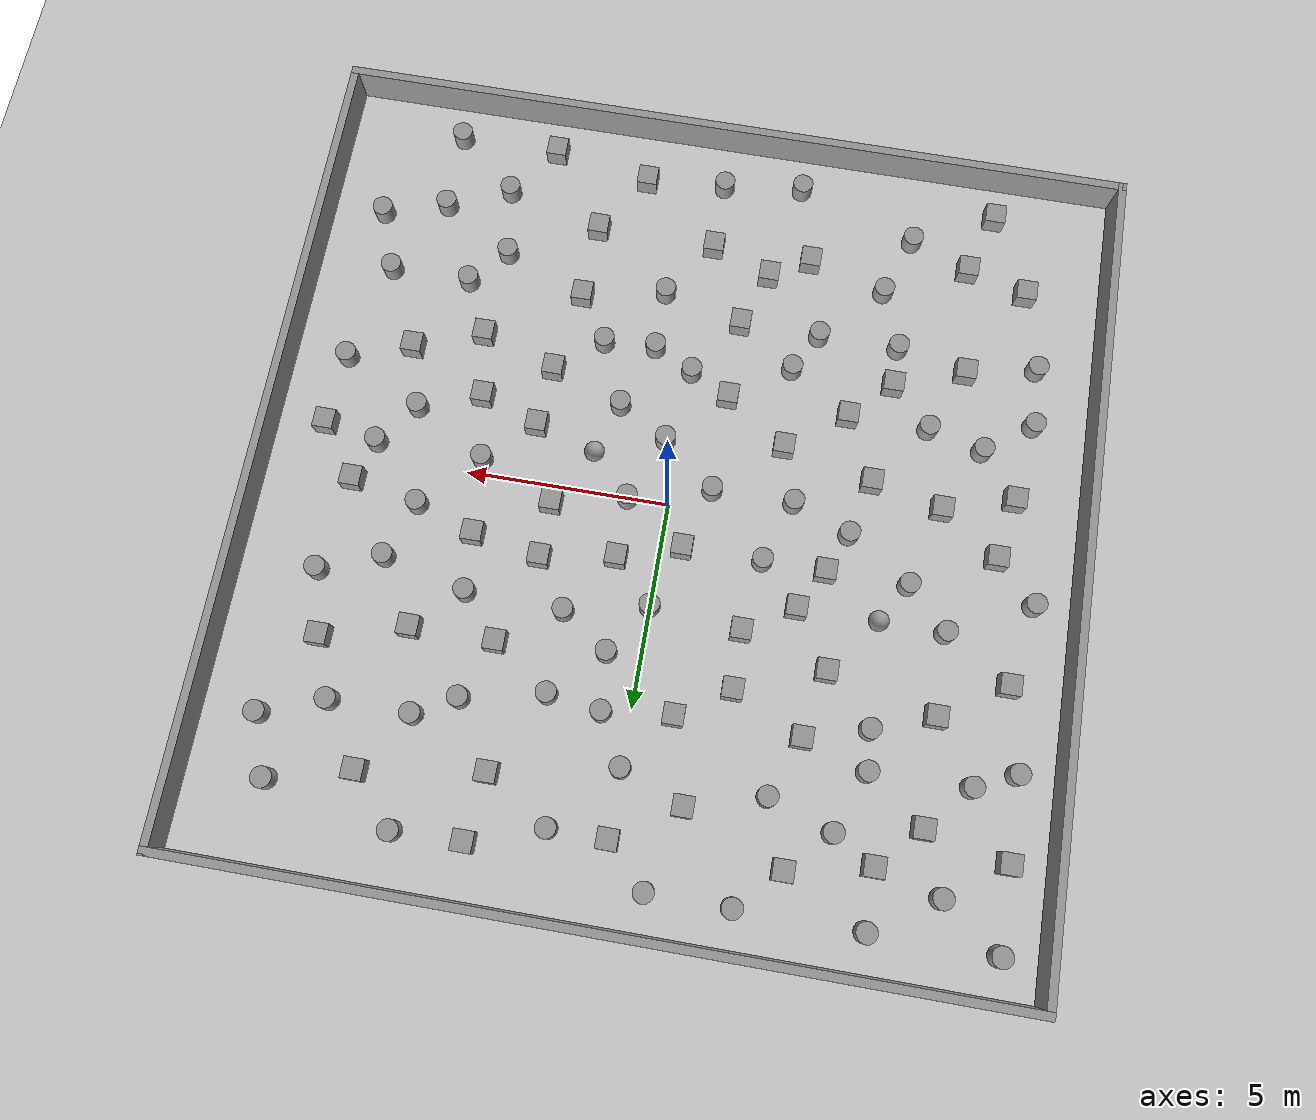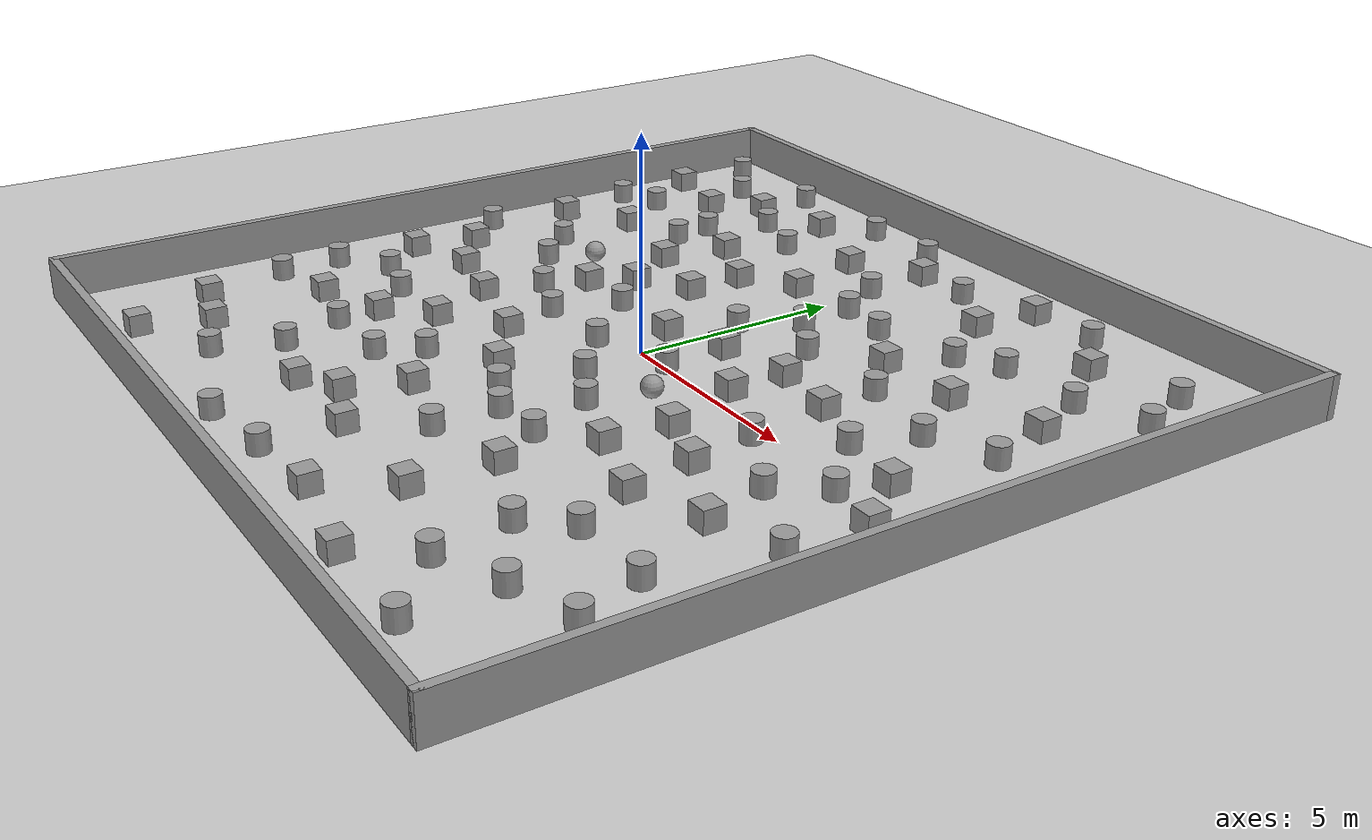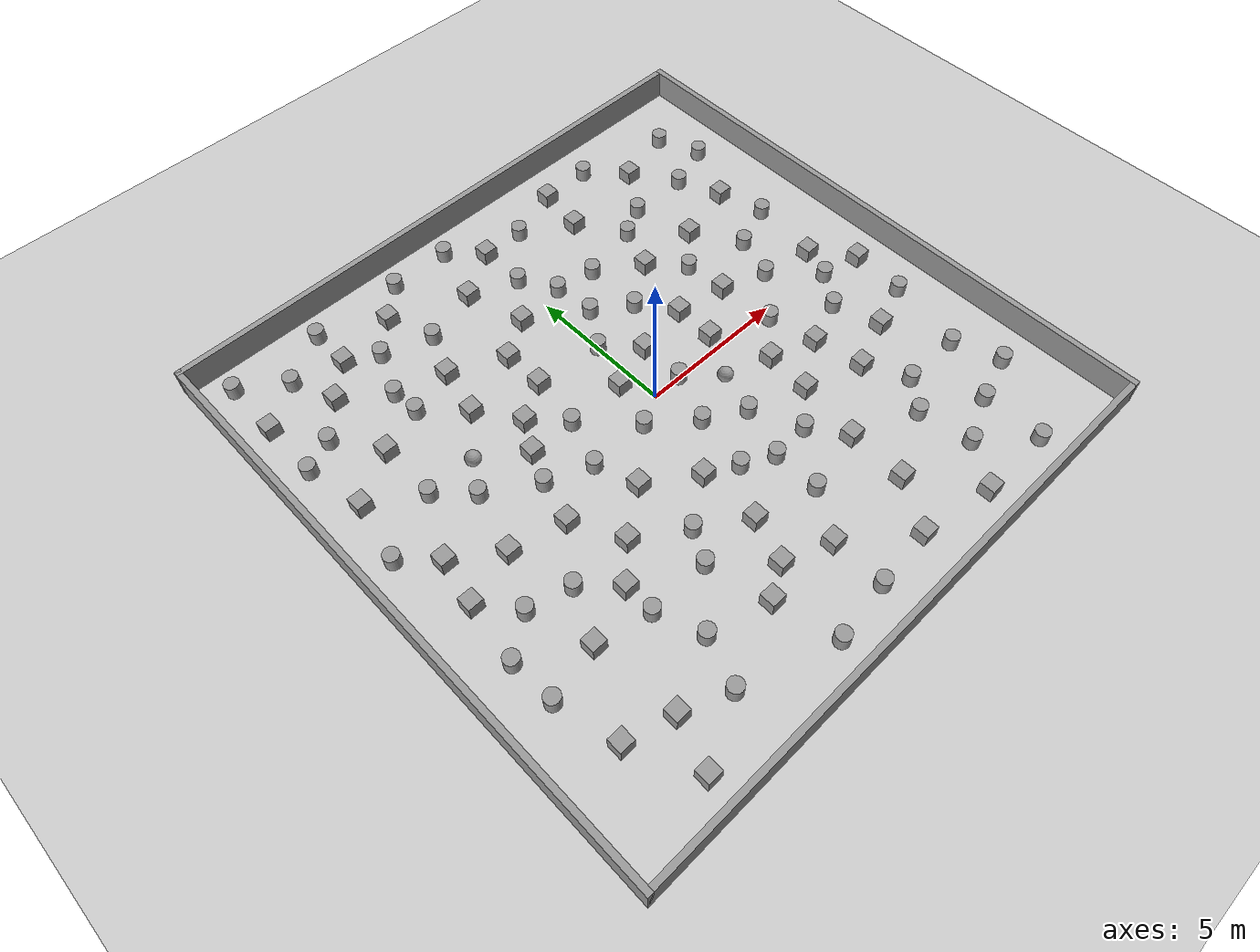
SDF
<sdf version="1.4">
 <world name="default">
  <light name="sun" type="directional">
   <pose>0 0 10 0 -0 0</pose>
   <diffuse>0.8 0.8 0.8 1</diffuse>
   <specular>0.2 0.2 0.2 1</specular>
   <attenuation>
    <range>1000</range>
    <constant>0.9</constant>
    <linear>0.01</linear>
    <quadratic>0.001</quadratic>
   </attenuation>
   <direction>-0.5 0.1 -0.9</direction>
  </light>
  <model name="ground_plane">
   <static>1</static>
   <link name="link">
    <collision name="collision">
     <geometry><plane><normal>0 0 1</normal><size>100 100</size></plane></geometry>
     <surface><friction><ode><mu>100</mu><mu2>50</mu2></ode></friction></surface>
    </collision>
    <visual name="visual">
     <cast_shadows>0</cast_shadows>
     <geometry><plane><normal>0 0 1</normal><size>100 100</size></plane></geometry>
     <material>
      <script><uri>file://media/materials/scripts/gazebo.material</uri><name>Gazebo/Grey</name></script>
     </material>
    </visual>
    <velocity_decay><linear>0</linear><angular>0</angular></velocity_decay>
   </link>
  </model>
  <physics type="ode">
   <max_step_size>0.001</max_step_size>
   <real_time_factor>1</real_time_factor>
   <real_time_update_rate>1000</real_time_update_rate>
   <gravity>0 0 -9.8</gravity>
  </physics>
  <scene><ambient>0.4 0.4 0.4 1</ambient><background>0.7 0.7 0.7 1</background><shadows>1</shadows></scene>
  <spherical_coordinates>
   <surface_model>EARTH_WGS84</surface_model>
   <latitude_deg>0</latitude_deg>
   <longitude_deg>0</longitude_deg>
   <elevation>0</elevation>
   <heading_deg>0</heading_deg>
  </spherical_coordinates>
  <model name="obstacle">
   <link name="Wall_0">
    <collision name="Wall_0_Collision">
     <geometry><box><size>20.2 0.2 1</size></box></geometry>
     <pose>0 0 0.5 0 -0 0</pose>
    </collision>
    <visual name="Wall_0_Visual">
     <pose>0 0 0.5 0 -0 0</pose>
     <geometry><box><size>20.2 0.2 1</size></box></geometry>
     <material>
      <script><uri>file://media/materials/scripts/gazebo.material</uri><name>Gazebo/Grey</name></script>
     </material>
    </visual>
    <velocity_decay><linear>0</linear><angular>0</angular></velocity_decay>
    <pose>10 0 0 0 -0 1.5708</pose>
   </link>
   <link name="Wall_1">
    <collision name="Wall_1_Collision">
     <geometry><box><size>20.2 0.2 1</size></box></geometry>
     <pose>0 0 0.5 0 -0 0</pose>
    </collision>
    <visual name="Wall_1_Visual">
     <pose>0 0 0.5 0 -0 0</pose>
     <geometry><box><size>20.2 0.2 1</size></box></geometry>
     <material>
      <script><uri>file://media/materials/scripts/gazebo.material</uri><name>Gazebo/Grey</name></script>
     </material>
    </visual>
    <velocity_decay><linear>0</linear><angular>0</angular></velocity_decay>
    <pose>0 10 0 0 -0 3.14159</pose>
   </link>
   <link name="Wall_2">
    <collision name="Wall_2_Collision">
     <geometry><box><size>20.2 0.2 1</size></box></geometry>
     <pose>0 0 0.5 0 -0 0</pose>
    </collision>
    <visual name="Wall_2_Visual">
     <pose>0 0 0.5 0 -0 0</pose>
     <geometry><box><size>20.2 0.2 1</size></box></geometry>
     <material>
      <script><uri>file://media/materials/scripts/gazebo.material</uri><name>Gazebo/Grey</name></script>
     </material>
    </visual>
    <velocity_decay><linear>0</linear><angular>0</angular></velocity_decay>
    <pose>-10 0 0 0 0 -1.5708</pose>
   </link>
   <link name="Wall_3">
    <collision name="Wall_3_Collision">
     <geometry><box><size>20.2 0.2 1</size></box></geometry>
     <pose>0 0 0.5 0 -0 0</pose>
    </collision>
    <visual name="Wall_3_Visual">
     <pose>0 0 0.5 0 -0 0</pose>
     <geometry><box><size>20.2 0.2 1</size></box></geometry>
     <material>
      <script><uri>file://media/materials/scripts/gazebo.material</uri><name>Gazebo/Grey</name></script>
     </material>
    </visual>
    <velocity_decay><linear>0</linear><angular>0</angular></velocity_decay>
    <pose>0 -10 0 0 -0 0</pose>
   </link>
   <static>1</static>
  </model>
  <model name="unit_cylinder_2">
   <pose>-6 1 0.25 0 -0 0</pose>
   <link name="link">
    <inertial>
     <mass>1</mass>
     <inertia><ixx>1</ixx><ixy>0</ixy><ixz>0</ixz><iyy>1</iyy><iyz>0</iyz><izz>1</izz></inertia>
    </inertial>
    <collision name="collision">
     <geometry><cylinder><radius>0.25</radius><length>0.5</length></cylinder></geometry>
    </collision>
    <visual name="visual">
     <geometry><cylinder><radius>0.25</radius><length>0.5</length></cylinder></geometry>
     <material>
      <script><uri>file://media/materials/scripts/gazebo.material</uri><name>Gazebo/Grey</name></script>
     </material>
    </visual>
    <velocity_decay><linear>0</linear><angular>0</angular></velocity_decay>
   </link>
   <static>0</static>
  </model>
  <model name="unit_box_1">
   <pose>3.07223 -5.09197 0.25 0 1e-06 1e-06</pose>
   <link name="link">
    <inertial>
     <mass>1</mass>
     <inertia><ixx>1</ixx><ixy>0</ixy><ixz>0</ixz><iyy>1</iyy><iyz>0</iyz><izz>1</izz></inertia>
    </inertial>
    <collision name="collision"><geometry><box><size>0.5 0.5 0.5</size></box></geometry></collision>
    <visual name="visual">
     <geometry><box><size>0.5 0.5 0.5</size></box></geometry>
     <material>
      <script><uri>file://media/materials/scripts/gazebo.material</uri><name>Gazebo/Grey</name></script>
     </material>
    </visual>
    <velocity_decay><linear>0</linear><angular>0</angular></velocity_decay>
   </link>
   <static>0</static>
  </model>
  <model name="unit_box_2">
   <pose>-8 -7 0.249999 -2e-06 1e-06 -1e-06</pose>
   <link name="link">
    <inertial>
     <mass>1</mass>
     <inertia><ixx>1</ixx><ixy>0</ixy><ixz>0</ixz><iyy>1</iyy><iyz>0</iyz><izz>1</izz></inertia>
    </inertial>
    <collision name="collision"><geometry><box><size>0.5 0.5 0.5</size></box></geometry></collision>
    <visual name="visual">
     <geometry><box><size>0.5 0.5 0.5</size></box></geometry>
     <material>
      <script><uri>file://media/materials/scripts/gazebo.material</uri><name>Gazebo/Grey</name></script>
     </material>
    </visual>
    <velocity_decay><linear>0</linear><angular>0</angular></velocity_decay>
   </link>
   <static>0</static>
  </model>
  <model name="unit_cylinder_3">
   <pose>5 6 0.25 0 -0 0</pose>
   <link name="link">
    <inertial>
     <mass>1</mass>
     <inertia><ixx>1</ixx><ixy>0</ixy><ixz>0</ixz><iyy>1</iyy><iyz>0</iyz><izz>1</izz></inertia>
    </inertial>
    <collision name="collision">
     <geometry><cylinder><radius>0.25</radius><length>0.5</length></cylinder></geometry>
    </collision>
    <visual name="visual">
     <geometry><cylinder><radius>0.25</radius><length>0.5</length></cylinder></geometry>
     <material>
      <script><uri>file://media/materials/scripts/gazebo.material</uri><name>Gazebo/Grey</name></script>
     </material>
    </visual>
    <velocity_decay><linear>0</linear><angular>0</angular></velocity_decay>
   </link>
   <static>0</static>
  </model>
  <model name="unit_cylinder_4">
   <pose>-7.58549 8 0.25 0 -0 0</pose>
   <link name="link">
    <inertial>
     <mass>1</mass>
     <inertia><ixx>1</ixx><ixy>0</ixy><ixz>0</ixz><iyy>1</iyy><iyz>0</iyz><izz>1</izz></inertia>
    </inertial>
    <collision name="collision">
     <geometry><cylinder><radius>0.25</radius><length>0.5</length></cylinder></geometry>
    </collision>
    <visual name="visual">
     <geometry><cylinder><radius>0.25</radius><length>0.5</length></cylinder></geometry>
     <material>
      <script><uri>file://media/materials/scripts/gazebo.material</uri><name>Gazebo/Grey</name></script>
     </material>
    </visual>
    <velocity_decay><linear>0</linear><angular>0</angular></velocity_decay>
   </link>
   <static>0</static>
  </model>
  <model name="unit_cylinder_5">
   <pose>7.3318 -0.384496 0.249991 0 -0 0</pose>
   <link name="link">
    <inertial>
     <mass>1</mass>
     <inertia><ixx>1</ixx><ixy>0</ixy><ixz>0</ixz><iyy>1</iyy><iyz>0</iyz><izz>1</izz></inertia>
    </inertial>
    <collision name="collision">
     <geometry><cylinder><radius>0.25</radius><length>0.5</length></cylinder></geometry>
    </collision>
    <visual name="visual">
     <geometry><cylinder><radius>0.25</radius><length>0.5</length></cylinder></geometry>
     <material>
      <script><uri>file://media/materials/scripts/gazebo.material</uri><name>Gazebo/Grey</name></script>
     </material>
    </visual>
    <velocity_decay><linear>0</linear><angular>0</angular></velocity_decay>
   </link>
   <static>0</static>
  </model>
  <model name="unit_cylinder_6">
   <pose>-5 -8 0.25 0 -0 0</pose>
   <link name="link">
    <inertial>
     <mass>1</mass>
     <inertia><ixx>1</ixx><ixy>0</ixy><ixz>0</ixz><iyy>1</iyy><iyz>0</iyz><izz>1</izz></inertia>
    </inertial>
    <collision name="collision">
     <geometry><cylinder><radius>0.25</radius><length>0.5</length></cylinder></geometry>
    </collision>
    <visual name="visual">
     <geometry><cylinder><radius>0.25</radius><length>0.5</length></cylinder></geometry>
     <material>
      <script><uri>file://media/materials/scripts/gazebo.material</uri><name>Gazebo/Grey</name></script>
     </material>
    </visual>
    <velocity_decay><linear>0</linear><angular>0</angular></velocity_decay>
   </link>
   <static>0</static>
  </model>
  <model name="unit_cylinder_7">
   <pose>-7.37957 -2.65 0.249991 0 -0 0</pose>
   <link name="link">
    <inertial>
     <mass>1</mass>
     <inertia><ixx>1</ixx><ixy>0</ixy><ixz>0</ixz><iyy>1</iyy><iyz>0</iyz><izz>1</izz></inertia>
    </inertial>
    <collision name="collision">
     <geometry><cylinder><radius>0.25</radius><length>0.5</length></cylinder></geometry>
    </collision>
    <visual name="visual">
     <geometry><cylinder><radius>0.25</radius><length>0.5</length></cylinder></geometry>
     <material>
      <script><uri>file://media/materials/scripts/gazebo.material</uri><name>Gazebo/Grey</name></script>
     </material>
    </visual>
    <velocity_decay><linear>0</linear><angular>0</angular></velocity_decay>
   </link>
   <static>0</static>
  </model>
  <model name="unit_cylinder_8">
   <pose>-5 7 0.25 0 -0 0</pose>
   <link name="link">
    <inertial>
     <mass>1</mass>
     <inertia><ixx>1</ixx><ixy>0</ixy><ixz>0</ixz><iyy>1</iyy><iyz>0</iyz><izz>1</izz></inertia>
    </inertial>
    <collision name="collision">
     <geometry><cylinder><radius>0.25</radius><length>0.5</length></cylinder></geometry>
    </collision>
    <visual name="visual">
     <geometry><cylinder><radius>0.25</radius><length>0.5</length></cylinder></geometry>
     <material>
      <script><uri>file://media/materials/scripts/gazebo.material</uri><name>Gazebo/Grey</name></script>
     </material>
    </visual>
    <velocity_decay><linear>0</linear><angular>0</angular></velocity_decay>
   </link>
   <static>0</static>
  </model>
  <model name="unit_cylinder_9">
   <pose>1.413 8 0.25 0 -0 0</pose>
   <link name="link">
    <inertial>
     <mass>1</mass>
     <inertia><ixx>1</ixx><ixy>0</ixy><ixz>0</ixz><iyy>1</iyy><iyz>0</iyz><izz>1</izz></inertia>
    </inertial>
    <collision name="collision">
     <geometry><cylinder><radius>0.25</radius><length>0.5</length></cylinder></geometry>
    </collision>
    <visual name="visual">
     <geometry><cylinder><radius>0.25</radius><length>0.5</length></cylinder></geometry>
     <material>
      <script><uri>file://media/materials/scripts/gazebo.material</uri><name>Gazebo/Grey</name></script>
     </material>
    </visual>
    <velocity_decay><linear>0</linear><angular>0</angular></velocity_decay>
   </link>
   <static>0</static>
  </model>
  <model name="unit_cylinder_10">
   <pose>8 8 0.25 0 -0 0</pose>
   <link name="link">
    <inertial>
     <mass>1</mass>
     <inertia><ixx>1</ixx><ixy>0</ixy><ixz>0</ixz><iyy>1</iyy><iyz>0</iyz><izz>1</izz></inertia>
    </inertial>
    <collision name="collision">
     <geometry><cylinder><radius>0.25</radius><length>0.5</length></cylinder></geometry>
    </collision>
    <visual name="visual">
     <geometry><cylinder><radius>0.25</radius><length>0.5</length></cylinder></geometry>
     <material>
      <script><uri>file://media/materials/scripts/gazebo.material</uri><name>Gazebo/Grey</name></script>
     </material>
    </visual>
    <velocity_decay><linear>0</linear><angular>0</angular></velocity_decay>
   </link>
   <static>0</static>
  </model>
  <model name="unit_cylinder_11">
   <pose>7 -7 0.25 0 -0 0</pose>
   <link name="link">
    <inertial>
     <mass>1</mass>
     <inertia><ixx>1</ixx><ixy>0</ixy><ixz>0</ixz><iyy>1</iyy><iyz>0</iyz><izz>1</izz></inertia>
    </inertial>
    <collision name="collision">
     <geometry><cylinder><radius>0.25</radius><length>0.5</length></cylinder></geometry>
    </collision>
    <visual name="visual">
     <geometry><cylinder><radius>0.25</radius><length>0.5</length></cylinder></geometry>
     <material>
      <script><uri>file://media/materials/scripts/gazebo.material</uri><name>Gazebo/Grey</name></script>
     </material>
    </visual>
    <velocity_decay><linear>0</linear><angular>0</angular></velocity_decay>
   </link>
   <static>0</static>
  </model>
  <model name="unit_box_3">
   <pose>5.50427 4 0.249999 1e-06 2e-06 -3e-06</pose>
   <link name="link">
    <inertial>
     <mass>1</mass>
     <inertia><ixx>1</ixx><ixy>0</ixy><ixz>0</ixz><iyy>1</iyy><iyz>0</iyz><izz>1</izz></inertia>
    </inertial>
    <collision name="collision"><geometry><box><size>0.5 0.5 0.5</size></box></geometry></collision>
    <visual name="visual">
     <geometry><box><size>0.5 0.5 0.5</size></box></geometry>
     <material>
      <script><uri>file://media/materials/scripts/gazebo.material</uri><name>Gazebo/Grey</name></script>
     </material>
    </visual>
    <velocity_decay><linear>0</linear><angular>0</angular></velocity_decay>
   </link>
   <static>0</static>
  </model>
  <model name="unit_box_4">
   <pose>-2.23419 2.75958 0.25 -1e-06 1e-06 1e-06</pose>
   <link name="link">
    <inertial>
     <mass>1</mass>
     <inertia><ixx>1</ixx><ixy>0</ixy><ixz>0</ixz><iyy>1</iyy><iyz>0</iyz><izz>1</izz></inertia>
    </inertial>
    <collision name="collision"><geometry><box><size>0.5 0.5 0.5</size></box></geometry></collision>
    <visual name="visual">
     <geometry><box><size>0.5 0.5 0.5</size></box></geometry>
     <material>
      <script><uri>file://media/materials/scripts/gazebo.material</uri><name>Gazebo/Grey</name></script>
     </material>
    </visual>
    <velocity_decay><linear>0</linear><angular>0</angular></velocity_decay>
   </link>
   <static>0</static>
  </model>
  <model name="unit_box_5">
   <pose>-7 4 0.249999 1e-06 2e-06 -3e-06</pose>
   <link name="link">
    <inertial>
     <mass>1</mass>
     <inertia><ixx>1</ixx><ixy>0</ixy><ixz>0</ixz><iyy>1</iyy><iyz>0</iyz><izz>1</izz></inertia>
    </inertial>
    <collision name="collision"><geometry><box><size>0.5 0.5 0.5</size></box></geometry></collision>
    <visual name="visual">
     <geometry><box><size>0.5 0.5 0.5</size></box></geometry>
     <material>
      <script><uri>file://media/materials/scripts/gazebo.material</uri><name>Gazebo/Grey</name></script>
     </material>
    </visual>
    <velocity_decay><linear>0</linear><angular>0</angular></velocity_decay>
   </link>
   <static>0</static>
  </model>
  <model name="unit_box_6">
   <pose>-1.55694 7 0.249999 -2e-06 -1e-06 1e-06</pose>
   <link name="link">
    <inertial>
     <mass>1</mass>
     <inertia><ixx>1</ixx><ixy>0</ixy><ixz>0</ixz><iyy>1</iyy><iyz>0</iyz><izz>1</izz></inertia>
    </inertial>
    <collision name="collision"><geometry><box><size>0.5 0.5 0.5</size></box></geometry></collision>
    <visual name="visual">
     <geometry><box><size>0.5 0.5 0.5</size></box></geometry>
     <material>
      <script><uri>file://media/materials/scripts/gazebo.material</uri><name>Gazebo/Grey</name></script>
     </material>
    </visual>
    <velocity_decay><linear>0</linear><angular>0</angular></velocity_decay>
   </link>
   <static>0</static>
  </model>
  <model name="unit_box_7">
   <pose>-4 5 0.249999 -2e-06 8.07794e-28 1e-06</pose>
   <link name="link">
    <inertial>
     <mass>1</mass>
     <inertia><ixx>1</ixx><ixy>0</ixy><ixz>0</ixz><iyy>1</iyy><iyz>0</iyz><izz>1</izz></inertia>
    </inertial>
    <collision name="collision"><geometry><box><size>0.5 0.5 0.5</size></box></geometry></collision>
    <visual name="visual">
     <geometry><box><size>0.5 0.5 0.5</size></box></geometry>
     <material>
      <script><uri>file://media/materials/scripts/gazebo.material</uri><name>Gazebo/Grey</name></script>
     </material>
    </visual>
    <velocity_decay><linear>0</linear><angular>0</angular></velocity_decay>
   </link>
   <static>0</static>
  </model>
  <model name="unit_box_8">
   <pose>5 -2 0.249999 -2e-06 -1e-06 -3e-06</pose>
   <link name="link">
    <inertial>
     <mass>1</mass>
     <inertia><ixx>1</ixx><ixy>0</ixy><ixz>0</ixz><iyy>1</iyy><iyz>0</iyz><izz>1</izz></inertia>
    </inertial>
    <collision name="collision"><geometry><box><size>0.5 0.5 0.5</size></box></geometry></collision>
    <visual name="visual">
     <geometry><box><size>0.5 0.5 0.5</size></box></geometry>
     <material>
      <script><uri>file://media/materials/scripts/gazebo.material</uri><name>Gazebo/Grey</name></script>
     </material>
    </visual>
    <velocity_decay><linear>0</linear><angular>0</angular></velocity_decay>
   </link>
   <static>0</static>
  </model>
  <model name="unit_box_9">
   <pose>-4 -3 0.249999 1e-06 1e-06 0</pose>
   <link name="link">
    <inertial>
     <mass>1</mass>
     <inertia><ixx>1</ixx><ixy>0</ixy><ixz>0</ixz><iyy>1</iyy><iyz>0</iyz><izz>1</izz></inertia>
    </inertial>
    <collision name="collision"><geometry><box><size>0.5 0.5 0.5</size></box></geometry></collision>
    <visual name="visual">
     <geometry><box><size>0.5 0.5 0.5</size></box></geometry>
     <material>
      <script><uri>file://media/materials/scripts/gazebo.material</uri><name>Gazebo/Grey</name></script>
     </material>
    </visual>
    <velocity_decay><linear>0</linear><angular>0</angular></velocity_decay>
   </link>
   <static>0</static>
  </model>
  <model name="unit_box_10">
   <pose>3 -7 0.249999 -1e-06 -2e-06 1e-06</pose>
   <link name="link">
    <inertial>
     <mass>1</mass>
     <inertia><ixx>1</ixx><ixy>0</ixy><ixz>0</ixz><iyy>1</iyy><iyz>0</iyz><izz>1</izz></inertia>
    </inertial>
    <collision name="collision"><geometry><box><size>0.5 0.5 0.5</size></box></geometry></collision>
    <visual name="visual">
     <geometry><box><size>0.5 0.5 0.5</size></box></geometry>
     <material>
      <script><uri>file://media/materials/scripts/gazebo.material</uri><name>Gazebo/Grey</name></script>
     </material>
    </visual>
    <velocity_decay><linear>0</linear><angular>0</angular></velocity_decay>
   </link>
   <static>0</static>
  </model>
  <model name="unit_cylinder_12">
   <pose>-0 -8.74103 0.249999 -0 -0 -0</pose>
   <link name="link">
    <inertial>
     <mass>1</mass>
     <inertia><ixx>1</ixx><ixy>0</ixy><ixz>0</ixz><iyy>1</iyy><iyz>0</iyz><izz>1</izz></inertia>
    </inertial>
    <collision name="collision">
     <geometry><cylinder><radius>0.25</radius><length>0.5</length></cylinder></geometry>
    </collision>
    <visual name="visual">
     <geometry><cylinder><radius>0.25</radius><length>0.5</length></cylinder></geometry>
     <material>
      <script><uri>file://media/materials/scripts/gazebo.material</uri><name>Gazebo/Grey</name></script>
     </material>
    </visual>
    <velocity_decay><linear>0</linear><angular>0</angular></velocity_decay>
   </link>
   <static>0</static>
  </model>
  <model name="unit_box_11">
   <pose>-2.50033 -7 0.249999 -1e-06 -2e-06 1e-06</pose>
   <link name="link">
    <inertial>
     <mass>1</mass>
     <inertia><ixx>1</ixx><ixy>0</ixy><ixz>0</ixz><iyy>1</iyy><iyz>0</iyz><izz>1</izz></inertia>
    </inertial>
    <collision name="collision"><geometry><box><size>0.5 0.5 0.5</size></box></geometry></collision>
    <visual name="visual">
     <geometry><box><size>0.5 0.5 0.5</size></box></geometry>
     <material>
      <script><uri>file://media/materials/scripts/gazebo.material</uri><name>Gazebo/Grey</name></script>
     </material>
    </visual>
    <velocity_decay><linear>0</linear><angular>0</angular></velocity_decay>
   </link>
   <static>0</static>
  </model>
  <model name="unit_cylinder_13">
   <pose>8 3 0.25 0 -0 0</pose>
   <link name="link">
    <inertial>
     <mass>1</mass>
     <inertia><ixx>1</ixx><ixy>0</ixy><ixz>0</ixz><iyy>1</iyy><iyz>0</iyz><izz>1</izz></inertia>
    </inertial>
    <collision name="collision">
     <geometry><cylinder><radius>0.25</radius><length>0.5</length></cylinder></geometry>
    </collision>
    <visual name="visual">
     <geometry><cylinder><radius>0.25</radius><length>0.5</length></cylinder></geometry>
     <material>
      <script><uri>file://media/materials/scripts/gazebo.material</uri><name>Gazebo/Grey</name></script>
     </material>
    </visual>
    <velocity_decay><linear>0</linear><angular>0</angular></velocity_decay>
   </link>
   <static>0</static>
  </model>
  <model name="unit_cylinder_14">
   <pose>2 5 0.249999 -0 -0 -0</pose>
   <link name="link">
    <inertial>
     <mass>1</mass>
     <inertia><ixx>1</ixx><ixy>0</ixy><ixz>0</ixz><iyy>1</iyy><iyz>0</iyz><izz>1</izz></inertia>
    </inertial>
    <collision name="collision">
     <geometry><cylinder><radius>0.25</radius><length>0.5</length></cylinder></geometry>
    </collision>
    <visual name="visual">
     <geometry><cylinder><radius>0.25</radius><length>0.5</length></cylinder></geometry>
     <material>
      <script><uri>file://media/materials/scripts/gazebo.material</uri><name>Gazebo/Grey</name></script>
     </material>
    </visual>
    <velocity_decay><linear>0</linear><angular>0</angular></velocity_decay>
   </link>
   <static>0</static>
  </model>
  <model name="unit_cylinder_15">
   <pose>0 2.5525 0.25 0 -0 0</pose>
   <link name="link">
    <inertial>
     <mass>1</mass>
     <inertia><ixx>1</ixx><ixy>0</ixy><ixz>0</ixz><iyy>1</iyy><iyz>0</iyz><izz>1</izz></inertia>
    </inertial>
    <collision name="collision">
     <geometry><cylinder><radius>0.25</radius><length>0.5</length></cylinder></geometry>
    </collision>
    <visual name="visual">
     <geometry><cylinder><radius>0.25</radius><length>0.5</length></cylinder></geometry>
     <material>
      <script><uri>file://media/materials/scripts/gazebo.material</uri><name>Gazebo/Grey</name></script>
     </material>
    </visual>
    <velocity_decay><linear>0</linear><angular>0</angular></velocity_decay>
   </link>
   <static>0</static>
  </model>
  <model name="unit_box_12">
   <pose>2.81797 1.80018 0.249999 -1e-06 -1e-06 0</pose>
   <link name="link">
    <inertial>
     <mass>1</mass>
     <inertia><ixx>1</ixx><ixy>0</ixy><ixz>0</ixz><iyy>1</iyy><iyz>0</iyz><izz>1</izz></inertia>
    </inertial>
    <collision name="collision"><geometry><box><size>0.5 0.5 0.5</size></box></geometry></collision>
    <visual name="visual">
     <geometry><box><size>0.5 0.5 0.5</size></box></geometry>
     <material>
      <script><uri>file://media/materials/scripts/gazebo.material</uri><name>Gazebo/Grey</name></script>
     </material>
    </visual>
    <velocity_decay><linear>0</linear><angular>0</angular></velocity_decay>
   </link>
   <static>0</static>
  </model>
  <model name="unit_cylinder_16">
   <pose>-3 -0.561679 0.25 0 -0 0</pose>
   <link name="link">
    <inertial>
     <mass>1</mass>
     <inertia><ixx>1</ixx><ixy>0</ixy><ixz>0</ixz><iyy>1</iyy><iyz>0</iyz><izz>1</izz></inertia>
    </inertial>
    <collision name="collision">
     <geometry><cylinder><radius>0.25</radius><length>0.5</length></cylinder></geometry>
    </collision>
    <visual name="visual">
     <geometry><cylinder><radius>0.25</radius><length>0.5</length></cylinder></geometry>
     <material>
      <script><uri>file://media/materials/scripts/gazebo.material</uri><name>Gazebo/Grey</name></script>
     </material>
    </visual>
    <velocity_decay><linear>0</linear><angular>0</angular></velocity_decay>
   </link>
   <static>0</static>
  </model>
  <model name="unit_box_13">
   <pose>-0.999999 -3 0.249999 2e-06 1e-06 8.07794e-28</pose>
   <link name="link">
    <inertial>
     <mass>1</mass>
     <inertia><ixx>1</ixx><ixy>0</ixy><ixz>0</ixz><iyy>1</iyy><iyz>0</iyz><izz>1</izz></inertia>
    </inertial>
    <collision name="collision"><geometry><box><size>0.5 0.5 0.5</size></box></geometry></collision>
    <visual name="visual">
     <geometry><box><size>0.5 0.5 0.5</size></box></geometry>
     <material>
      <script><uri>file://media/materials/scripts/gazebo.material</uri><name>Gazebo/Grey</name></script>
     </material>
    </visual>
    <velocity_decay><linear>0</linear><angular>0</angular></velocity_decay>
   </link>
   <static>0</static>
  </model>
  <model name="unit_cylinder_17">
   <pose>1.5915 -2.34142 0.249999 -0 -0 -0</pose>
   <link name="link">
    <inertial>
     <mass>1</mass>
     <inertia><ixx>1</ixx><ixy>0</ixy><ixz>0</ixz><iyy>1</iyy><iyz>0</iyz><izz>1</izz></inertia>
    </inertial>
    <collision name="collision">
     <geometry><cylinder><radius>0.25</radius><length>0.5</length></cylinder></geometry>
    </collision>
    <visual name="visual">
     <geometry><cylinder><radius>0.25</radius><length>0.5</length></cylinder></geometry>
     <material>
      <script><uri>file://media/materials/scripts/gazebo.material</uri><name>Gazebo/Grey</name></script>
     </material>
    </visual>
    <velocity_decay><linear>0</linear><angular>0</angular></velocity_decay>
   </link>
   <static>0</static>
  </model>
  <model name="unit_cylinder_18">
   <pose>1 -5.52202 0.249999 -0 -0 -0</pose>
   <link name="link">
    <inertial>
     <mass>1</mass>
     <inertia><ixx>1</ixx><ixy>0</ixy><ixz>0</ixz><iyy>1</iyy><iyz>0</iyz><izz>1</izz></inertia>
    </inertial>
    <collision name="collision">
     <geometry><cylinder><radius>0.25</radius><length>0.5</length></cylinder></geometry>
    </collision>
    <visual name="visual">
     <geometry><cylinder><radius>0.25</radius><length>0.5</length></cylinder></geometry>
     <material>
      <script><uri>file://media/materials/scripts/gazebo.material</uri><name>Gazebo/Grey</name></script>
     </material>
    </visual>
    <velocity_decay><linear>0</linear><angular>0</angular></velocity_decay>
   </link>
   <static>0</static>
  </model>
  <model name="unit_cylinder_19">
   <pose>-5 -5 0.249999 -0 -0 -0</pose>
   <link name="link">
    <inertial>
     <mass>1</mass>
     <inertia><ixx>1</ixx><ixy>0</ixy><ixz>0</ixz><iyy>1</iyy><iyz>0</iyz><izz>1</izz></inertia>
    </inertial>
    <collision name="collision">
     <geometry><cylinder><radius>0.25</radius><length>0.5</length></cylinder></geometry>
    </collision>
    <visual name="visual">
     <geometry><cylinder><radius>0.25</radius><length>0.5</length></cylinder></geometry>
     <material>
      <script><uri>file://media/materials/scripts/gazebo.material</uri><name>Gazebo/Grey</name></script>
     </material>
    </visual>
    <velocity_decay><linear>0</linear><angular>0</angular></velocity_decay>
   </link>
   <static>0</static>
  </model>
  <model name="unit_box_14">
   <pose>-8 1e-06 0.249999 -1e-06 2e-06 1e-06</pose>
   <link name="link">
    <inertial>
     <mass>1</mass>
     <inertia><ixx>1</ixx><ixy>0</ixy><ixz>0</ixz><iyy>1</iyy><iyz>0</iyz><izz>1</izz></inertia>
    </inertial>
    <collision name="collision"><geometry><box><size>0.5 0.5 0.5</size></box></geometry></collision>
    <visual name="visual">
     <geometry><box><size>0.5 0.5 0.5</size></box></geometry>
     <material>
      <script><uri>file://media/materials/scripts/gazebo.material</uri><name>Gazebo/Grey</name></script>
     </material>
    </visual>
    <velocity_decay><linear>0</linear><angular>0</angular></velocity_decay>
   </link>
   <static>0</static>
  </model>
  <model name="unit_cylinder_20">
   <pose>8 -5 0.25 0 -0 0</pose>
   <link name="link">
    <inertial>
     <mass>1</mass>
     <inertia><ixx>1</ixx><ixy>0</ixy><ixz>0</ixz><iyy>1</iyy><iyz>0</iyz><izz>1</izz></inertia>
    </inertial>
    <collision name="collision">
     <geometry><cylinder><radius>0.25</radius><length>0.5</length></cylinder></geometry>
    </collision>
    <visual name="visual">
     <geometry><cylinder><radius>0.25</radius><length>0.5</length></cylinder></geometry>
     <material>
      <script><uri>file://media/materials/scripts/gazebo.material</uri><name>Gazebo/Grey</name></script>
     </material>
    </visual>
    <velocity_decay><linear>0</linear><angular>0</angular></velocity_decay>
   </link>
   <static>0</static>
  </model>
  <model name="unit_box_15">
   <pose>8.674 -0.655566 0.249999 1e-06 2e-06 2e-06</pose>
   <link name="link">
    <inertial>
     <mass>1</mass>
     <inertia><ixx>1</ixx><ixy>0</ixy><ixz>0</ixz><iyy>1</iyy><iyz>0</iyz><izz>1</izz></inertia>
    </inertial>
    <collision name="collision"><geometry><box><size>0.5 0.5 0.5</size></box></geometry></collision>
    <visual name="visual">
     <geometry><box><size>0.5 0.5 0.5</size></box></geometry>
     <material>
      <script><uri>file://media/materials/scripts/gazebo.material</uri><name>Gazebo/Grey</name></script>
     </material>
    </visual>
    <velocity_decay><linear>0</linear><angular>0</angular></velocity_decay>
   </link>
   <static>0</static>
  </model>
  <model name="unit_cylinder_21">
   <pose>6 1 0.25 0 -0 0</pose>
   <link name="link">
    <inertial>
     <mass>1</mass>
     <inertia><ixx>1</ixx><ixy>0</ixy><ixz>0</ixz><iyy>1</iyy><iyz>0</iyz><izz>1</izz></inertia>
    </inertial>
    <collision name="collision">
     <geometry><cylinder><radius>0.25</radius><length>0.5</length></cylinder></geometry>
    </collision>
    <visual name="visual">
     <geometry><cylinder><radius>0.25</radius><length>0.5</length></cylinder></geometry>
     <material>
      <script><uri>file://media/materials/scripts/gazebo.material</uri><name>Gazebo/Grey</name></script>
     </material>
    </visual>
    <velocity_decay><linear>0</linear><angular>0</angular></velocity_decay>
   </link>
   <static>0</static>
  </model>
  <model name="unit_box_16">
   <pose>7 -3 0.249999 -1e-06 -2e-06 -3e-06</pose>
   <link name="link">
    <inertial>
     <mass>1</mass>
     <inertia><ixx>1</ixx><ixy>0</ixy><ixz>0</ixz><iyy>1</iyy><iyz>0</iyz><izz>1</izz></inertia>
    </inertial>
    <collision name="collision"><geometry><box><size>0.5 0.5 0.5</size></box></geometry></collision>
    <visual name="visual">
     <geometry><box><size>0.5 0.5 0.5</size></box></geometry>
     <material>
      <script><uri>file://media/materials/scripts/gazebo.material</uri><name>Gazebo/Grey</name></script>
     </material>
    </visual>
    <velocity_decay><linear>0</linear><angular>0</angular></velocity_decay>
   </link>
   <static>0</static>
  </model>
  <model name="unit_cylinder_1">
   <pose>-1 -0.544952 0.25 0 -0 0</pose>
   <link name="link">
    <inertial>
     <mass>1</mass>
     <inertia><ixx>1</ixx><ixy>0</ixy><ixz>0</ixz><iyy>1</iyy><iyz>0</iyz><izz>1</izz></inertia>
    </inertial>
    <collision name="collision">
     <geometry><cylinder><radius>0.25</radius><length>0.5</length></cylinder></geometry>
    </collision>
    <visual name="visual">
     <geometry><cylinder><radius>0.25</radius><length>0.5</length></cylinder></geometry>
     <material>
      <script><uri>file://media/materials/scripts/gazebo.material</uri><name>Gazebo/Grey</name></script>
     </material>
    </visual>
    <velocity_decay><linear>0</linear><angular>0</angular></velocity_decay>
   </link>
   <static>0</static>
  </model>
  <model name="unit_box_1_0">
   <pose>-0.518956 0.999999 0.249999 1e-06 -2e-06 -3e-06</pose>
   <link name="link">
    <inertial>
     <mass>1</mass>
     <inertia><ixx>1</ixx><ixy>0</ixy><ixz>0</ixz><iyy>1</iyy><iyz>0</iyz><izz>1</izz></inertia>
    </inertial>
    <collision name="collision"><geometry><box><size>0.5 0.5 0.5</size></box></geometry></collision>
    <visual name="visual">
     <geometry><box><size>0.5 0.5 0.5</size></box></geometry>
     <material>
      <script><uri>file://media/materials/scripts/gazebo.material</uri><name>Gazebo/Grey</name></script>
     </material>
    </visual>
    <velocity_decay><linear>0</linear><angular>0</angular></velocity_decay>
   </link>
   <static>0</static>
  </model>
  <model name="unit_cylinder_2_0">
   <pose>1 0 0.25 0 -0 0</pose>
   <link name="link">
    <inertial>
     <mass>1</mass>
     <inertia><ixx>1</ixx><ixy>0</ixy><ixz>0</ixz><iyy>1</iyy><iyz>0</iyz><izz>1</izz></inertia>
    </inertial>
    <collision name="collision">
     <geometry><cylinder><radius>0.25</radius><length>0.5</length></cylinder></geometry>
    </collision>
    <visual name="visual">
     <geometry><cylinder><radius>0.25</radius><length>0.5</length></cylinder></geometry>
     <material>
      <script><uri>file://media/materials/scripts/gazebo.material</uri><name>Gazebo/Grey</name></script>
     </material>
    </visual>
    <velocity_decay><linear>0</linear><angular>0</angular></velocity_decay>
   </link>
   <static>0</static>
  </model>
  <model name="unit_cylinder_3_0">
   <pose>0.338659 -1.63315 0.249995 0 -0 0</pose>
   <link name="link">
    <inertial>
     <mass>1</mass>
     <inertia><ixx>1</ixx><ixy>0</ixy><ixz>0</ixz><iyy>1</iyy><iyz>0</iyz><izz>1</izz></inertia>
    </inertial>
    <collision name="collision">
     <geometry><cylinder><radius>0.25</radius><length>0.5</length></cylinder></geometry>
    </collision>
    <visual name="visual">
     <geometry><cylinder><radius>0.25</radius><length>0.5</length></cylinder></geometry>
     <material>
      <script><uri>file://media/materials/scripts/gazebo.material</uri><name>Gazebo/Grey</name></script>
     </material>
    </visual>
    <velocity_decay><linear>0</linear><angular>0</angular></velocity_decay>
   </link>
   <static>0</static>
  </model>
  <model name="unit_box_2_0">
   <pose>1 1.49539 0.249999 2e-06 1e-06 8.07794e-28</pose>
   <link name="link">
    <inertial>
     <mass>1</mass>
     <inertia><ixx>1</ixx><ixy>0</ixy><ixz>0</ixz><iyy>1</iyy><iyz>0</iyz><izz>1</izz></inertia>
    </inertial>
    <collision name="collision"><geometry><box><size>0.5 0.5 0.5</size></box></geometry></collision>
    <visual name="visual">
     <geometry><box><size>0.5 0.5 0.5</size></box></geometry>
     <material>
      <script><uri>file://media/materials/scripts/gazebo.material</uri><name>Gazebo/Grey</name></script>
     </material>
    </visual>
    <velocity_decay><linear>0</linear><angular>0</angular></velocity_decay>
   </link>
   <static>0</static>
  </model>
  <model name="unit_cylinder_4_0">
   <pose>-2.47034 1 0.25 0 -0 0</pose>
   <link name="link">
    <inertial>
     <mass>1</mass>
     <inertia><ixx>1</ixx><ixy>0</ixy><ixz>0</ixz><iyy>1</iyy><iyz>0</iyz><izz>1</izz></inertia>
    </inertial>
    <collision name="collision">
     <geometry><cylinder><radius>0.25</radius><length>0.5</length></cylinder></geometry>
    </collision>
    <visual name="visual">
     <geometry><cylinder><radius>0.25</radius><length>0.5</length></cylinder></geometry>
     <material>
      <script><uri>file://media/materials/scripts/gazebo.material</uri><name>Gazebo/Grey</name></script>
     </material>
    </visual>
    <velocity_decay><linear>0</linear><angular>0</angular></velocity_decay>
   </link>
   <static>0</static>
  </model>
  <model name="unit_box_3_0">
   <pose>-4.3515 3.37188 0.249999 -2e-06 1e-06 2e-06</pose>
   <link name="link">
    <inertial>
     <mass>1</mass>
     <inertia><ixx>1</ixx><ixy>0</ixy><ixz>0</ixz><iyy>1</iyy><iyz>0</iyz><izz>1</izz></inertia>
    </inertial>
    <collision name="collision"><geometry><box><size>0.5 0.5 0.5</size></box></geometry></collision>
    <visual name="visual">
     <geometry><box><size>0.5 0.5 0.5</size></box></geometry>
     <material>
      <script><uri>file://media/materials/scripts/gazebo.material</uri><name>Gazebo/Grey</name></script>
     </material>
    </visual>
    <velocity_decay><linear>0</linear><angular>0</angular></velocity_decay>
   </link>
   <static>0</static>
  </model>
  <model name="unit_cylinder_5_0">
   <pose>-7 2 0.25 0 -0 0</pose>
   <link name="link">
    <inertial>
     <mass>1</mass>
     <inertia><ixx>1</ixx><ixy>0</ixy><ixz>0</ixz><iyy>1</iyy><iyz>0</iyz><izz>1</izz></inertia>
    </inertial>
    <collision name="collision">
     <geometry><cylinder><radius>0.25</radius><length>0.5</length></cylinder></geometry>
    </collision>
    <visual name="visual">
     <geometry><cylinder><radius>0.25</radius><length>0.5</length></cylinder></geometry>
     <material>
      <script><uri>file://media/materials/scripts/gazebo.material</uri><name>Gazebo/Grey</name></script>
     </material>
    </visual>
    <velocity_decay><linear>0</linear><angular>0</angular></velocity_decay>
   </link>
   <static>0</static>
  </model>
  <model name="unit_box_4_0">
   <pose>-4.79758 -1.40389 0.249999 2e-06 1e-06 1e-06</pose>
   <link name="link">
    <inertial>
     <mass>1</mass>
     <inertia><ixx>1</ixx><ixy>0</ixy><ixz>0</ixz><iyy>1</iyy><iyz>0</iyz><izz>1</izz></inertia>
    </inertial>
    <collision name="collision"><geometry><box><size>0.5 0.5 0.5</size></box></geometry></collision>
    <visual name="visual">
     <geometry><box><size>0.5 0.5 0.5</size></box></geometry>
     <material>
      <script><uri>file://media/materials/scripts/gazebo.material</uri><name>Gazebo/Grey</name></script>
     </material>
    </visual>
    <velocity_decay><linear>0</linear><angular>0</angular></velocity_decay>
   </link>
   <static>0</static>
  </model>
  <model name="unit_box_5_0">
   <pose>-6.56142 -1 0.249999 2e-06 -8.07794e-28 1e-06</pose>
   <link name="link">
    <inertial>
     <mass>1</mass>
     <inertia><ixx>1</ixx><ixy>0</ixy><ixz>0</ixz><iyy>1</iyy><iyz>0</iyz><izz>1</izz></inertia>
    </inertial>
    <collision name="collision"><geometry><box><size>0.5 0.5 0.5</size></box></geometry></collision>
    <visual name="visual">
     <geometry><box><size>0.5 0.5 0.5</size></box></geometry>
     <material>
      <script><uri>file://media/materials/scripts/gazebo.material</uri><name>Gazebo/Grey</name></script>
     </material>
    </visual>
    <velocity_decay><linear>0</linear><angular>0</angular></velocity_decay>
   </link>
   <static>0</static>
  </model>
  <model name="unit_cylinder_6_0">
   <pose>-6 -3 0.25 0 -0 0</pose>
   <link name="link">
    <inertial>
     <mass>1</mass>
     <inertia><ixx>1</ixx><ixy>0</ixy><ixz>0</ixz><iyy>1</iyy><iyz>0</iyz><izz>1</izz></inertia>
    </inertial>
    <collision name="collision">
     <geometry><cylinder><radius>0.25</radius><length>0.5</length></cylinder></geometry>
    </collision>
    <visual name="visual">
     <geometry><cylinder><radius>0.25</radius><length>0.5</length></cylinder></geometry>
     <material>
      <script><uri>file://media/materials/scripts/gazebo.material</uri><name>Gazebo/Grey</name></script>
     </material>
    </visual>
    <velocity_decay><linear>0</linear><angular>0</angular></velocity_decay>
   </link>
   <static>0</static>
  </model>
  <model name="unit_box_6_0">
   <pose>-4 0.999999 0.25 1e-06 -1e-06 -1e-06</pose>
   <link name="link">
    <inertial>
     <mass>1</mass>
     <inertia><ixx>1</ixx><ixy>0</ixy><ixz>0</ixz><iyy>1</iyy><iyz>0</iyz><izz>1</izz></inertia>
    </inertial>
    <collision name="collision"><geometry><box><size>0.5 0.5 0.5</size></box></geometry></collision>
    <visual name="visual">
     <geometry><box><size>0.5 0.5 0.5</size></box></geometry>
     <material>
      <script><uri>file://media/materials/scripts/gazebo.material</uri><name>Gazebo/Grey</name></script>
     </material>
    </visual>
    <velocity_decay><linear>0</linear><angular>0</angular></velocity_decay>
   </link>
   <static>0</static>
  </model>
  <model name="unit_cylinder_7_0">
   <pose>-5.59398 5.514 0.25 0 -0 0</pose>
   <link name="link">
    <inertial>
     <mass>1</mass>
     <inertia><ixx>1</ixx><ixy>0</ixy><ixz>0</ixz><iyy>1</iyy><iyz>0</iyz><izz>1</izz></inertia>
    </inertial>
    <collision name="collision">
     <geometry><cylinder><radius>0.25</radius><length>0.5</length></cylinder></geometry>
    </collision>
    <visual name="visual">
     <geometry><cylinder><radius>0.25</radius><length>0.5</length></cylinder></geometry>
     <material>
      <script><uri>file://media/materials/scripts/gazebo.material</uri><name>Gazebo/Grey</name></script>
     </material>
    </visual>
    <velocity_decay><linear>0</linear><angular>0</angular></velocity_decay>
   </link>
   <static>0</static>
  </model>
  <model name="unit_box_7_0">
   <pose>-7 6.55811 0.249999 -2e-06 1e-06 1e-06</pose>
   <link name="link">
    <inertial>
     <mass>1</mass>
     <inertia><ixx>1</ixx><ixy>0</ixy><ixz>0</ixz><iyy>1</iyy><iyz>0</iyz><izz>1</izz></inertia>
    </inertial>
    <collision name="collision"><geometry><box><size>0.5 0.5 0.5</size></box></geometry></collision>
    <visual name="visual">
     <geometry><box><size>0.5 0.5 0.5</size></box></geometry>
     <material>
      <script><uri>file://media/materials/scripts/gazebo.material</uri><name>Gazebo/Grey</name></script>
     </material>
    </visual>
    <velocity_decay><linear>0</linear><angular>0</angular></velocity_decay>
   </link>
   <static>0</static>
  </model>
  <model name="unit_cylinder_8_0">
   <pose>-8 5.46484 0.25 0 -0 0</pose>
   <link name="link">
    <inertial>
     <mass>1</mass>
     <inertia><ixx>1</ixx><ixy>0</ixy><ixz>0</ixz><iyy>1</iyy><iyz>0</iyz><izz>1</izz></inertia>
    </inertial>
    <collision name="collision">
     <geometry><cylinder><radius>0.25</radius><length>0.5</length></cylinder></geometry>
    </collision>
    <visual name="visual">
     <geometry><cylinder><radius>0.25</radius><length>0.5</length></cylinder></geometry>
     <material>
      <script><uri>file://media/materials/scripts/gazebo.material</uri><name>Gazebo/Grey</name></script>
     </material>
    </visual>
    <velocity_decay><linear>0</linear><angular>0</angular></velocity_decay>
   </link>
   <static>0</static>
  </model>
  <model name="unit_box_8_0">
   <pose>-9 7 0.249999 -1e-06 2e-06 1e-06</pose>
   <link name="link">
    <inertial>
     <mass>1</mass>
     <inertia><ixx>1</ixx><ixy>0</ixy><ixz>0</ixz><iyy>1</iyy><iyz>0</iyz><izz>1</izz></inertia>
    </inertial>
    <collision name="collision"><geometry><box><size>0.5 0.5 0.5</size></box></geometry></collision>
    <visual name="visual">
     <geometry><box><size>0.5 0.5 0.5</size></box></geometry>
     <material>
      <script><uri>file://media/materials/scripts/gazebo.material</uri><name>Gazebo/Grey</name></script>
     </material>
    </visual>
    <velocity_decay><linear>0</linear><angular>0</angular></velocity_decay>
   </link>
   <static>0</static>
  </model>
  <model name="unit_cylinder_9_0">
   <pose>-9 5 0.25 0 -0 0</pose>
   <link name="link">
    <inertial>
     <mass>1</mass>
     <inertia><ixx>1</ixx><ixy>0</ixy><ixz>0</ixz><iyy>1</iyy><iyz>0</iyz><izz>1</izz></inertia>
    </inertial>
    <collision name="collision">
     <geometry><cylinder><radius>0.25</radius><length>0.5</length></cylinder></geometry>
    </collision>
    <visual name="visual">
     <geometry><cylinder><radius>0.25</radius><length>0.5</length></cylinder></geometry>
     <material>
      <script><uri>file://media/materials/scripts/gazebo.material</uri><name>Gazebo/Grey</name></script>
     </material>
    </visual>
    <velocity_decay><linear>0</linear><angular>0</angular></velocity_decay>
   </link>
   <static>0</static>
  </model>
  <model name="unit_box_9_0">
   <pose>-8.59861 3 0.249999 1e-06 -2e-06 -3e-06</pose>
   <link name="link">
    <inertial>
     <mass>1</mass>
     <inertia><ixx>1</ixx><ixy>0</ixy><ixz>0</ixz><iyy>1</iyy><iyz>0</iyz><izz>1</izz></inertia>
    </inertial>
    <collision name="collision"><geometry><box><size>0.5 0.5 0.5</size></box></geometry></collision>
    <visual name="visual">
     <geometry><box><size>0.5 0.5 0.5</size></box></geometry>
     <material>
      <script><uri>file://media/materials/scripts/gazebo.material</uri><name>Gazebo/Grey</name></script>
     </material>
    </visual>
    <velocity_decay><linear>0</linear><angular>0</angular></velocity_decay>
   </link>
   <static>0</static>
  </model>
  <model name="unit_cylinder_10_0">
   <pose>-6 9 0.25 0 -0 0</pose>
   <link name="link">
    <inertial>
     <mass>1</mass>
     <inertia><ixx>1</ixx><ixy>0</ixy><ixz>0</ixz><iyy>1</iyy><iyz>0</iyz><izz>1</izz></inertia>
    </inertial>
    <collision name="collision">
     <geometry><cylinder><radius>0.25</radius><length>0.5</length></cylinder></geometry>
    </collision>
    <visual name="visual">
     <geometry><cylinder><radius>0.25</radius><length>0.5</length></cylinder></geometry>
     <material>
      <script><uri>file://media/materials/scripts/gazebo.material</uri><name>Gazebo/Grey</name></script>
     </material>
    </visual>
    <velocity_decay><linear>0</linear><angular>0</angular></velocity_decay>
   </link>
   <static>0</static>
  </model>
  <model name="unit_cylinder_11_0">
   <pose>-9 9 0.25 0 -0 0</pose>
   <link name="link">
    <inertial>
     <mass>1</mass>
     <inertia><ixx>1</ixx><ixy>0</ixy><ixz>0</ixz><iyy>1</iyy><iyz>0</iyz><izz>1</izz></inertia>
    </inertial>
    <collision name="collision">
     <geometry><cylinder><radius>0.25</radius><length>0.5</length></cylinder></geometry>
    </collision>
    <visual name="visual">
     <geometry><cylinder><radius>0.25</radius><length>0.5</length></cylinder></geometry>
     <material>
      <script><uri>file://media/materials/scripts/gazebo.material</uri><name>Gazebo/Grey</name></script>
     </material>
    </visual>
    <velocity_decay><linear>0</linear><angular>0</angular></velocity_decay>
   </link>
   <static>0</static>
  </model>
  <model name="unit_box_10_0">
   <pose>-4 8 0.249999 -2e-06 1e-06 1e-06</pose>
   <link name="link">
    <inertial>
     <mass>1</mass>
     <inertia><ixx>1</ixx><ixy>0</ixy><ixz>0</ixz><iyy>1</iyy><iyz>0</iyz><izz>1</izz></inertia>
    </inertial>
    <collision name="collision"><geometry><box><size>0.5 0.5 0.5</size></box></geometry></collision>
    <visual name="visual">
     <geometry><box><size>0.5 0.5 0.5</size></box></geometry>
     <material>
      <script><uri>file://media/materials/scripts/gazebo.material</uri><name>Gazebo/Grey</name></script>
     </material>
    </visual>
    <velocity_decay><linear>0</linear><angular>0</angular></velocity_decay>
   </link>
   <static>0</static>
  </model>
  <model name="unit_cylinder_12_0">
   <pose>-3 9 0.25 0 -0 0</pose>
   <link name="link">
    <inertial>
     <mass>1</mass>
     <inertia><ixx>1</ixx><ixy>0</ixy><ixz>0</ixz><iyy>1</iyy><iyz>0</iyz><izz>1</izz></inertia>
    </inertial>
    <collision name="collision">
     <geometry><cylinder><radius>0.25</radius><length>0.5</length></cylinder></geometry>
    </collision>
    <visual name="visual">
     <geometry><cylinder><radius>0.25</radius><length>0.5</length></cylinder></geometry>
     <material>
      <script><uri>file://media/materials/scripts/gazebo.material</uri><name>Gazebo/Grey</name></script>
     </material>
    </visual>
    <velocity_decay><linear>0</linear><angular>0</angular></velocity_decay>
   </link>
   <static>0</static>
  </model>
  <model name="unit_box_11_0">
   <pose>-1 5 0.25 0 0 -2e-06</pose>
   <link name="link">
    <inertial>
     <mass>1</mass>
     <inertia><ixx>1</ixx><ixy>0</ixy><ixz>0</ixz><iyy>1</iyy><iyz>0</iyz><izz>1</izz></inertia>
    </inertial>
    <collision name="collision"><geometry><box><size>0.5 0.5 0.5</size></box></geometry></collision>
    <visual name="visual">
     <geometry><box><size>0.5 0.5 0.5</size></box></geometry>
     <material>
      <script><uri>file://media/materials/scripts/gazebo.material</uri><name>Gazebo/Grey</name></script>
     </material>
    </visual>
    <velocity_decay><linear>0</linear><angular>0</angular></velocity_decay>
   </link>
   <static>0</static>
  </model>
  <model name="unit_cylinder_13_0">
   <pose>-1 9 0.25 0 -0 0</pose>
   <link name="link">
    <inertial>
     <mass>1</mass>
     <inertia><ixx>1</ixx><ixy>0</ixy><ixz>0</ixz><iyy>1</iyy><iyz>0</iyz><izz>1</izz></inertia>
    </inertial>
    <collision name="collision">
     <geometry><cylinder><radius>0.25</radius><length>0.5</length></cylinder></geometry>
    </collision>
    <visual name="visual">
     <geometry><cylinder><radius>0.25</radius><length>0.5</length></cylinder></geometry>
     <material>
      <script><uri>file://media/materials/scripts/gazebo.material</uri><name>Gazebo/Grey</name></script>
     </material>
    </visual>
    <velocity_decay><linear>0</linear><angular>0</angular></velocity_decay>
   </link>
   <static>0</static>
  </model>
  <model name="unit_box_12_0">
   <pose>3.20226 8.59564 0.249999 1e-06 2e-06 8.07794e-28</pose>
   <link name="link">
    <inertial>
     <mass>1</mass>
     <inertia><ixx>1</ixx><ixy>0</ixy><ixz>0</ixz><iyy>1</iyy><iyz>0</iyz><izz>1</izz></inertia>
    </inertial>
    <collision name="collision"><geometry><box><size>0.5 0.5 0.5</size></box></geometry></collision>
    <visual name="visual">
     <geometry><box><size>0.5 0.5 0.5</size></box></geometry>
     <material>
      <script><uri>file://media/materials/scripts/gazebo.material</uri><name>Gazebo/Grey</name></script>
     </material>
    </visual>
    <velocity_decay><linear>0</linear><angular>0</angular></velocity_decay>
   </link>
   <static>0</static>
  </model>
  <model name="unit_cylinder_14_0">
   <pose>4.89793 8.64949 0.25 0 -0 0</pose>
   <link name="link">
    <inertial>
     <mass>1</mass>
     <inertia><ixx>1</ixx><ixy>0</ixy><ixz>0</ixz><iyy>1</iyy><iyz>0</iyz><izz>1</izz></inertia>
    </inertial>
    <collision name="collision">
     <geometry><cylinder><radius>0.25</radius><length>0.5</length></cylinder></geometry>
    </collision>
    <visual name="visual">
     <geometry><cylinder><radius>0.25</radius><length>0.5</length></cylinder></geometry>
     <material>
      <script><uri>file://media/materials/scripts/gazebo.material</uri><name>Gazebo/Grey</name></script>
     </material>
    </visual>
    <velocity_decay><linear>0</linear><angular>0</angular></velocity_decay>
   </link>
   <static>0</static>
  </model>
  <model name="unit_box_13_0">
   <pose>3 7 0.249999 -1e-06 -2e-06 1e-06</pose>
   <link name="link">
    <inertial>
     <mass>1</mass>
     <inertia><ixx>1</ixx><ixy>0</ixy><ixz>0</ixz><iyy>1</iyy><iyz>0</iyz><izz>1</izz></inertia>
    </inertial>
    <collision name="collision"><geometry><box><size>0.5 0.5 0.5</size></box></geometry></collision>
    <visual name="visual">
     <geometry><box><size>0.5 0.5 0.5</size></box></geometry>
     <material>
      <script><uri>file://media/materials/scripts/gazebo.material</uri><name>Gazebo/Grey</name></script>
     </material>
    </visual>
    <velocity_decay><linear>0</linear><angular>0</angular></velocity_decay>
   </link>
   <static>0</static>
  </model>
  <model name="unit_cylinder_15_0">
   <pose>0.007662 6.39032 0.249991 0 -0 0</pose>
   <link name="link">
    <inertial>
     <mass>1</mass>
     <inertia><ixx>1</ixx><ixy>0</ixy><ixz>0</ixz><iyy>1</iyy><iyz>0</iyz><izz>1</izz></inertia>
    </inertial>
    <collision name="collision">
     <geometry><cylinder><radius>0.25</radius><length>0.5</length></cylinder></geometry>
    </collision>
    <visual name="visual">
     <geometry><cylinder><radius>0.25</radius><length>0.5</length></cylinder></geometry>
     <material>
      <script><uri>file://media/materials/scripts/gazebo.material</uri><name>Gazebo/Grey</name></script>
     </material>
    </visual>
    <velocity_decay><linear>0</linear><angular>0</angular></velocity_decay>
   </link>
   <static>0</static>
  </model>
  <model name="unit_box_14_0">
   <pose>6 7.46069 0.249999 -2e-06 1e-06 3e-06</pose>
   <link name="link">
    <inertial>
     <mass>1</mass>
     <inertia><ixx>1</ixx><ixy>0</ixy><ixz>0</ixz><iyy>1</iyy><iyz>0</iyz><izz>1</izz></inertia>
    </inertial>
    <collision name="collision"><geometry><box><size>0.5 0.5 0.5</size></box></geometry></collision>
    <visual name="visual">
     <geometry><box><size>0.5 0.5 0.5</size></box></geometry>
     <material>
      <script><uri>file://media/materials/scripts/gazebo.material</uri><name>Gazebo/Grey</name></script>
     </material>
    </visual>
    <velocity_decay><linear>0</linear><angular>0</angular></velocity_decay>
   </link>
   <static>0</static>
  </model>
  <model name="unit_cylinder_16_0">
   <pose>2 3 0.25 0 -0 0</pose>
   <link name="link">
    <inertial>
     <mass>1</mass>
     <inertia><ixx>1</ixx><ixy>0</ixy><ixz>0</ixz><iyy>1</iyy><iyz>0</iyz><izz>1</izz></inertia>
    </inertial>
    <collision name="collision">
     <geometry><cylinder><radius>0.25</radius><length>0.5</length></cylinder></geometry>
    </collision>
    <visual name="visual">
     <geometry><cylinder><radius>0.25</radius><length>0.5</length></cylinder></geometry>
     <material>
      <script><uri>file://media/materials/scripts/gazebo.material</uri><name>Gazebo/Grey</name></script>
     </material>
    </visual>
    <velocity_decay><linear>0</linear><angular>0</angular></velocity_decay>
   </link>
   <static>0</static>
  </model>
  <model name="unit_box_16_0">
   <pose>2.79825 0.427417 0.25 -1e-06 1e-06 2e-06</pose>
   <link name="link">
    <inertial>
     <mass>1</mass>
     <inertia><ixx>1</ixx><ixy>0</ixy><ixz>0</ixz><iyy>1</iyy><iyz>0</iyz><izz>1</izz></inertia>
    </inertial>
    <collision name="collision"><geometry><box><size>0.5 0.5 0.5</size></box></geometry></collision>
    <visual name="visual">
     <geometry><box><size>0.5 0.5 0.5</size></box></geometry>
     <material>
      <script><uri>file://media/materials/scripts/gazebo.material</uri><name>Gazebo/Grey</name></script>
     </material>
    </visual>
    <velocity_decay><linear>0</linear><angular>0</angular></velocity_decay>
   </link>
   <static>0</static>
  </model>
  <model name="unit_cylinder_17_0">
   <pose>4.39855 2.93832 0.249991 0 -0 0</pose>
   <link name="link">
    <inertial>
     <mass>1</mass>
     <inertia><ixx>1</ixx><ixy>0</ixy><ixz>0</ixz><iyy>1</iyy><iyz>0</iyz><izz>1</izz></inertia>
    </inertial>
    <collision name="collision">
     <geometry><cylinder><radius>0.25</radius><length>0.5</length></cylinder></geometry>
    </collision>
    <visual name="visual">
     <geometry><cylinder><radius>0.25</radius><length>0.5</length></cylinder></geometry>
     <material>
      <script><uri>file://media/materials/scripts/gazebo.material</uri><name>Gazebo/Grey</name></script>
     </material>
    </visual>
    <velocity_decay><linear>0</linear><angular>0</angular></velocity_decay>
   </link>
   <static>0</static>
  </model>
  <model name="unit_box_17">
   <pose>3.4362 4 0.25 -2e-06 -0 -3e-06</pose>
   <link name="link">
    <inertial>
     <mass>1</mass>
     <inertia><ixx>1</ixx><ixy>0</ixy><ixz>0</ixz><iyy>1</iyy><iyz>0</iyz><izz>1</izz></inertia>
    </inertial>
    <collision name="collision"><geometry><box><size>0.5 0.5 0.5</size></box></geometry></collision>
    <visual name="visual">
     <geometry><box><size>0.5 0.5 0.5</size></box></geometry>
     <material>
      <script><uri>file://media/materials/scripts/gazebo.material</uri><name>Gazebo/Grey</name></script>
     </material>
    </visual>
    <velocity_decay><linear>0</linear><angular>0</angular></velocity_decay>
   </link>
   <static>0</static>
  </model>
  <model name="unit_cylinder_18_0">
   <pose>0.8137 3.80518 0.249991 0 -0 0</pose>
   <link name="link">
    <inertial>
     <mass>1</mass>
     <inertia><ixx>1</ixx><ixy>0</ixy><ixz>0</ixz><iyy>1</iyy><iyz>0</iyz><izz>1</izz></inertia>
    </inertial>
    <collision name="collision">
     <geometry><cylinder><radius>0.25</radius><length>0.5</length></cylinder></geometry>
    </collision>
    <visual name="visual">
     <geometry><cylinder><radius>0.25</radius><length>0.5</length></cylinder></geometry>
     <material>
      <script><uri>file://media/materials/scripts/gazebo.material</uri><name>Gazebo/Grey</name></script>
     </material>
    </visual>
    <velocity_decay><linear>0</linear><angular>0</angular></velocity_decay>
   </link>
   <static>0</static>
  </model>
  <model name="unit_cylinder_19_0">
   <pose>-8.48394 -5 0.25 0 -0 0</pose>
   <link name="link">
    <inertial>
     <mass>1</mass>
     <inertia><ixx>1</ixx><ixy>0</ixy><ixz>0</ixz><iyy>1</iyy><iyz>0</iyz><izz>1</izz></inertia>
    </inertial>
    <collision name="collision">
     <geometry><cylinder><radius>0.25</radius><length>0.5</length></cylinder></geometry>
    </collision>
    <visual name="visual">
     <geometry><cylinder><radius>0.25</radius><length>0.5</length></cylinder></geometry>
     <material>
      <script><uri>file://media/materials/scripts/gazebo.material</uri><name>Gazebo/Grey</name></script>
     </material>
    </visual>
    <velocity_decay><linear>0</linear><angular>0</angular></velocity_decay>
   </link>
   <static>0</static>
  </model>
  <model name="unit_box_18">
   <pose>-6.73354 -4.63038 0.249999 2e-06 -1e-06 -8.07794e-28</pose>
   <link name="link">
    <inertial>
     <mass>1</mass>
     <inertia><ixx>1</ixx><ixy>0</ixy><ixz>0</ixz><iyy>1</iyy><iyz>0</iyz><izz>1</izz></inertia>
    </inertial>
    <collision name="collision"><geometry><box><size>0.5 0.5 0.5</size></box></geometry></collision>
    <visual name="visual">
     <geometry><box><size>0.5 0.5 0.5</size></box></geometry>
     <material>
      <script><uri>file://media/materials/scripts/gazebo.material</uri><name>Gazebo/Grey</name></script>
     </material>
    </visual>
    <velocity_decay><linear>0</linear><angular>0</angular></velocity_decay>
   </link>
   <static>0</static>
  </model>
  <model name="unit_cylinder_20_0">
   <pose>-3 -5 0.25 0 -0 0</pose>
   <link name="link">
    <inertial>
     <mass>1</mass>
     <inertia><ixx>1</ixx><ixy>0</ixy><ixz>0</ixz><iyy>1</iyy><iyz>0</iyz><izz>1</izz></inertia>
    </inertial>
    <collision name="collision">
     <geometry><cylinder><radius>0.25</radius><length>0.5</length></cylinder></geometry>
    </collision>
    <visual name="visual">
     <geometry><cylinder><radius>0.25</radius><length>0.5</length></cylinder></geometry>
     <material>
      <script><uri>file://media/materials/scripts/gazebo.material</uri><name>Gazebo/Grey</name></script>
     </material>
    </visual>
    <velocity_decay><linear>0</linear><angular>0</angular></velocity_decay>
   </link>
   <static>0</static>
  </model>
  <model name="unit_box_19">
   <pose>-7 -9 0.249999 2e-06 -1e-06 -1e-06</pose>
   <link name="link">
    <inertial>
     <mass>1</mass>
     <inertia><ixx>1</ixx><ixy>0</ixy><ixz>0</ixz><iyy>1</iyy><iyz>0</iyz><izz>1</izz></inertia>
    </inertial>
    <collision name="collision"><geometry><box><size>0.5 0.5 0.5</size></box></geometry></collision>
    <visual name="visual">
     <geometry><box><size>0.5 0.5 0.5</size></box></geometry>
     <material>
      <script><uri>file://media/materials/scripts/gazebo.material</uri><name>Gazebo/Grey</name></script>
     </material>
    </visual>
    <velocity_decay><linear>0</linear><angular>0</angular></velocity_decay>
   </link>
   <static>0</static>
  </model>
  <model name="unit_cylinder_21_0">
   <pose>7 6 0.25 0 -0 0</pose>
   <link name="link">
    <inertial>
     <mass>1</mass>
     <inertia><ixx>1</ixx><ixy>0</ixy><ixz>0</ixz><iyy>1</iyy><iyz>0</iyz><izz>1</izz></inertia>
    </inertial>
    <collision name="collision">
     <geometry><cylinder><radius>0.25</radius><length>0.5</length></cylinder></geometry>
    </collision>
    <visual name="visual">
     <geometry><cylinder><radius>0.25</radius><length>0.5</length></cylinder></geometry>
     <material>
      <script><uri>file://media/materials/scripts/gazebo.material</uri><name>Gazebo/Grey</name></script>
     </material>
    </visual>
    <velocity_decay><linear>0</linear><angular>0</angular></velocity_decay>
   </link>
   <static>0</static>
  </model>
  <model name="unit_box_20">
   <pose>-1 -5 0.25 0 0 -2e-06</pose>
   <link name="link">
    <inertial>
     <mass>1</mass>
     <inertia><ixx>1</ixx><ixy>0</ixy><ixz>0</ixz><iyy>1</iyy><iyz>0</iyz><izz>1</izz></inertia>
    </inertial>
    <collision name="collision"><geometry><box><size>0.5 0.5 0.5</size></box></geometry></collision>
    <visual name="visual">
     <geometry><box><size>0.5 0.5 0.5</size></box></geometry>
     <material>
      <script><uri>file://media/materials/scripts/gazebo.material</uri><name>Gazebo/Grey</name></script>
     </material>
    </visual>
    <velocity_decay><linear>0</linear><angular>0</angular></velocity_decay>
   </link>
   <static>0</static>
  </model>
  <model name="unit_cylinder_22">
   <pose>1 -4 0.25 0 -0 0</pose>
   <link name="link">
    <inertial>
     <mass>1</mass>
     <inertia><ixx>1</ixx><ixy>0</ixy><ixz>0</ixz><iyy>1</iyy><iyz>0</iyz><izz>1</izz></inertia>
    </inertial>
    <collision name="collision">
     <geometry><cylinder><radius>0.25</radius><length>0.5</length></cylinder></geometry>
    </collision>
    <visual name="visual">
     <geometry><cylinder><radius>0.25</radius><length>0.5</length></cylinder></geometry>
     <material>
      <script><uri>file://media/materials/scripts/gazebo.material</uri><name>Gazebo/Grey</name></script>
     </material>
    </visual>
    <velocity_decay><linear>0</linear><angular>0</angular></velocity_decay>
   </link>
   <static>0</static>
  </model>
  <model name="unit_box_21">
   <pose>3.41119 -3 0.249999 -1e-06 -2e-06 -4e-06</pose>
   <link name="link">
    <inertial>
     <mass>1</mass>
     <inertia><ixx>1</ixx><ixy>0</ixy><ixz>0</ixz><iyy>1</iyy><iyz>0</iyz><izz>1</izz></inertia>
    </inertial>
    <collision name="collision"><geometry><box><size>0.5 0.5 0.5</size></box></geometry></collision>
    <visual name="visual">
     <geometry><box><size>0.5 0.5 0.5</size></box></geometry>
     <material>
      <script><uri>file://media/materials/scripts/gazebo.material</uri><name>Gazebo/Grey</name></script>
     </material>
    </visual>
    <velocity_decay><linear>0</linear><angular>0</angular></velocity_decay>
   </link>
   <static>0</static>
  </model>
  <model name="unit_cylinder_23">
   <pose>6 -5 0.25 0 -0 0</pose>
   <link name="link">
    <inertial>
     <mass>1</mass>
     <inertia><ixx>1</ixx><ixy>0</ixy><ixz>0</ixz><iyy>1</iyy><iyz>0</iyz><izz>1</izz></inertia>
    </inertial>
    <collision name="collision">
     <geometry><cylinder><radius>0.25</radius><length>0.5</length></cylinder></geometry>
    </collision>
    <visual name="visual">
     <geometry><cylinder><radius>0.25</radius><length>0.5</length></cylinder></geometry>
     <material>
      <script><uri>file://media/materials/scripts/gazebo.material</uri><name>Gazebo/Grey</name></script>
     </material>
    </visual>
    <velocity_decay><linear>0</linear><angular>0</angular></velocity_decay>
   </link>
   <static>0</static>
  </model>
  <model name="unit_box_22">
   <pose>-0 -7 0.249999 -1e-06 -2e-06 3e-06</pose>
   <link name="link">
    <inertial>
     <mass>1</mass>
     <inertia><ixx>1</ixx><ixy>0</ixy><ixz>0</ixz><iyy>1</iyy><iyz>0</iyz><izz>1</izz></inertia>
    </inertial>
    <collision name="collision"><geometry><box><size>0.5 0.5 0.5</size></box></geometry></collision>
    <visual name="visual">
     <geometry><box><size>0.5 0.5 0.5</size></box></geometry>
     <material>
      <script><uri>file://media/materials/scripts/gazebo.material</uri><name>Gazebo/Grey</name></script>
     </material>
    </visual>
    <velocity_decay><linear>0</linear><angular>0</angular></velocity_decay>
   </link>
   <static>0</static>
  </model>
  <model name="unit_cylinder_24">
   <pose>5.45457 -7.66774 0.249999 -0 -0 -0</pose>
   <link name="link">
    <inertial>
     <mass>1</mass>
     <inertia><ixx>1</ixx><ixy>0</ixy><ixz>0</ixz><iyy>1</iyy><iyz>0</iyz><izz>1</izz></inertia>
    </inertial>
    <collision name="collision">
     <geometry><cylinder><radius>0.25</radius><length>0.5</length></cylinder></geometry>
    </collision>
    <visual name="visual">
     <geometry><cylinder><radius>0.25</radius><length>0.5</length></cylinder></geometry>
     <material>
      <script><uri>file://media/materials/scripts/gazebo.material</uri><name>Gazebo/Grey</name></script>
     </material>
    </visual>
    <velocity_decay><linear>0</linear><angular>0</angular></velocity_decay>
   </link>
   <static>0</static>
  </model>
  <model name="unit_box_23">
   <pose>2 -8.56932 0.249999 2e-06 1e-06 8.07794e-28</pose>
   <link name="link">
    <inertial>
     <mass>1</mass>
     <inertia><ixx>1</ixx><ixy>0</ixy><ixz>0</ixz><iyy>1</iyy><iyz>0</iyz><izz>1</izz></inertia>
    </inertial>
    <collision name="collision"><geometry><box><size>0.5 0.5 0.5</size></box></geometry></collision>
    <visual name="visual">
     <geometry><box><size>0.5 0.5 0.5</size></box></geometry>
     <material>
      <script><uri>file://media/materials/scripts/gazebo.material</uri><name>Gazebo/Grey</name></script>
     </material>
    </visual>
    <velocity_decay><linear>0</linear><angular>0</angular></velocity_decay>
   </link>
   <static>0</static>
  </model>
  <model name="unit_cylinder_25">
   <pose>-2 -9 0.25 0 -0 0</pose>
   <link name="link">
    <inertial>
     <mass>1</mass>
     <inertia><ixx>1</ixx><ixy>0</ixy><ixz>0</ixz><iyy>1</iyy><iyz>0</iyz><izz>1</izz></inertia>
    </inertial>
    <collision name="collision">
     <geometry><cylinder><radius>0.25</radius><length>0.5</length></cylinder></geometry>
    </collision>
    <visual name="visual">
     <geometry><cylinder><radius>0.25</radius><length>0.5</length></cylinder></geometry>
     <material>
      <script><uri>file://media/materials/scripts/gazebo.material</uri><name>Gazebo/Grey</name></script>
     </material>
    </visual>
    <velocity_decay><linear>0</linear><angular>0</angular></velocity_decay>
   </link>
   <static>0</static>
  </model>
  <model name="unit_box_24">
   <pose>4.47047 -9 0.249999 -1e-06 -2e-06 2e-06</pose>
   <link name="link">
    <inertial>
     <mass>1</mass>
     <inertia><ixx>1</ixx><ixy>0</ixy><ixz>0</ixz><iyy>1</iyy><iyz>0</iyz><izz>1</izz></inertia>
    </inertial>
    <collision name="collision"><geometry><box><size>0.5 0.5 0.5</size></box></geometry></collision>
    <visual name="visual">
     <geometry><box><size>0.5 0.5 0.5</size></box></geometry>
     <material>
      <script><uri>file://media/materials/scripts/gazebo.material</uri><name>Gazebo/Grey</name></script>
     </material>
    </visual>
    <velocity_decay><linear>0</linear><angular>0</angular></velocity_decay>
   </link>
   <static>0</static>
  </model>
  <model name="unit_cylinder_26">
   <pose>7 -9 0.25 0 -0 0</pose>
   <link name="link">
    <inertial>
     <mass>1</mass>
     <inertia><ixx>1</ixx><ixy>0</ixy><ixz>0</ixz><iyy>1</iyy><iyz>0</iyz><izz>1</izz></inertia>
    </inertial>
    <collision name="collision">
     <geometry><cylinder><radius>0.25</radius><length>0.5</length></cylinder></geometry>
    </collision>
    <visual name="visual">
     <geometry><cylinder><radius>0.25</radius><length>0.5</length></cylinder></geometry>
     <material>
      <script><uri>file://media/materials/scripts/gazebo.material</uri><name>Gazebo/Grey</name></script>
     </material>
    </visual>
    <velocity_decay><linear>0</linear><angular>0</angular></velocity_decay>
   </link>
   <static>0</static>
  </model>
  <model name="unit_cylinder_27">
   <pose>4.68576 -0.39227 0.249991 0 -0 0</pose>
   <link name="link">
    <inertial>
     <mass>1</mass>
     <inertia><ixx>1</ixx><ixy>0</ixy><ixz>0</ixz><iyy>1</iyy><iyz>0</iyz><izz>1</izz></inertia>
    </inertial>
    <collision name="collision">
     <geometry><cylinder><radius>0.25</radius><length>0.5</length></cylinder></geometry>
    </collision>
    <visual name="visual">
     <geometry><cylinder><radius>0.25</radius><length>0.5</length></cylinder></geometry>
     <material>
      <script><uri>file://media/materials/scripts/gazebo.material</uri><name>Gazebo/Grey</name></script>
     </material>
    </visual>
    <velocity_decay><linear>0</linear><angular>0</angular></velocity_decay>
   </link>
   <static>0</static>
  </model>
  <model name="unit_box_25">
   <pose>7.6868 0.654672 0.249999 -1e-06 2e-06 3e-06</pose>
   <link name="link">
    <inertial>
     <mass>1</mass>
     <inertia><ixx>1</ixx><ixy>0</ixy><ixz>0</ixz><iyy>1</iyy><iyz>0</iyz><izz>1</izz></inertia>
    </inertial>
    <collision name="collision"><geometry><box><size>0.5 0.5 0.5</size></box></geometry></collision>
    <visual name="visual">
     <geometry><box><size>0.5 0.5 0.5</size></box></geometry>
     <material>
      <script><uri>file://media/materials/scripts/gazebo.material</uri><name>Gazebo/Grey</name></script>
     </material>
    </visual>
    <velocity_decay><linear>0</linear><angular>0</angular></velocity_decay>
   </link>
   <static>0</static>
  </model>
  <model name="unit_box_1_1">
   <pose>-2.55798 -1.94079 0.249999 1e-06 -1e-06 0</pose>
   <link name="link">
    <inertial>
     <mass>1</mass>
     <inertia><ixx>1</ixx><ixy>0</ixy><ixz>0</ixz><iyy>1</iyy><iyz>0</iyz><izz>1</izz></inertia>
    </inertial>
    <collision name="collision"><geometry><box><size>0.5 0.5 0.5</size></box></geometry></collision>
    <visual name="visual">
     <geometry><box><size>0.5 0.5 0.5</size></box></geometry>
     <material>
      <script><uri>file://media/materials/scripts/gazebo.material</uri><name>Gazebo/Grey</name></script>
     </material>
    </visual>
    <velocity_decay><linear>0</linear><angular>0</angular></velocity_decay>
   </link>
   <static>0</static>
  </model>
  <model name="unit_box_2_1">
   <pose>-5 -4 0.25 0 0 -1e-06</pose>
   <link name="link">
    <inertial>
     <mass>1</mass>
     <inertia><ixx>1</ixx><ixy>0</ixy><ixz>0</ixz><iyy>1</iyy><iyz>0</iyz><izz>1</izz></inertia>
    </inertial>
    <collision name="collision"><geometry><box><size>0.5 0.5 0.5</size></box></geometry></collision>
    <visual name="visual">
     <geometry><box><size>0.5 0.5 0.5</size></box></geometry>
     <material>
      <script><uri>file://media/materials/scripts/gazebo.material</uri><name>Gazebo/Grey</name></script>
     </material>
    </visual>
    <velocity_decay><linear>0</linear><angular>0</angular></velocity_decay>
   </link>
   <static>0</static>
  </model>
  <model name="unit_box_3_1">
   <pose>-3.44149 2 0.249999 1e-06 -2e-06 -8.07794e-28</pose>
   <link name="link">
    <inertial>
     <mass>1</mass>
     <inertia><ixx>1</ixx><ixy>0</ixy><ixz>0</ixz><iyy>1</iyy><iyz>0</iyz><izz>1</izz></inertia>
    </inertial>
    <collision name="collision"><geometry><box><size>0.5 0.5 0.5</size></box></geometry></collision>
    <visual name="visual">
     <geometry><box><size>0.5 0.5 0.5</size></box></geometry>
     <material>
      <script><uri>file://media/materials/scripts/gazebo.material</uri><name>Gazebo/Grey</name></script>
     </material>
    </visual>
    <velocity_decay><linear>0</linear><angular>0</angular></velocity_decay>
   </link>
   <static>0</static>
  </model>
  <model name="unit_sphere_1">
   <pose>-5.40387 2 0.25 0 -0 0</pose>
   <link name="link">
    <inertial>
     <mass>1</mass>
     <inertia><ixx>1</ixx><ixy>0</ixy><ixz>0</ixz><iyy>1</iyy><iyz>0</iyz><izz>1</izz></inertia>
    </inertial>
    <collision name="collision"><geometry><sphere><radius>0.25</radius></sphere></geometry></collision>
    <visual name="visual">
     <geometry><sphere><radius>0.25</radius></sphere></geometry>
     <material>
      <script><uri>file://media/materials/scripts/gazebo.material</uri><name>Gazebo/Grey</name></script>
     </material>
    </visual>
    <velocity_decay><linear>0</linear><angular>0</angular></velocity_decay>
   </link>
   <static>0</static>
  </model>
  <model name="unit_box_4_1">
   <pose>-2.25192 4.1699 0.249999 2e-06 -1e-06 -1e-06</pose>
   <link name="link">
    <inertial>
     <mass>1</mass>
     <inertia><ixx>1</ixx><ixy>0</ixy><ixz>0</ixz><iyy>1</iyy><iyz>0</iyz><izz>1</izz></inertia>
    </inertial>
    <collision name="collision"><geometry><box><size>0.5 0.5 0.5</size></box></geometry></collision>
    <visual name="visual">
     <geometry><box><size>0.5 0.5 0.5</size></box></geometry>
     <material>
      <script><uri>file://media/materials/scripts/gazebo.material</uri><name>Gazebo/Grey</name></script>
     </material>
    </visual>
    <velocity_decay><linear>0</linear><angular>0</angular></velocity_decay>
   </link>
   <static>0</static>
  </model>
  <model name="unit_sphere_2">
   <pose>2 -1 0.25 0 -0 0</pose>
   <link name="link">
    <inertial>
     <mass>1</mass>
     <inertia><ixx>1</ixx><ixy>0</ixy><ixz>0</ixz><iyy>1</iyy><iyz>0</iyz><izz>1</izz></inertia>
    </inertial>
    <collision name="collision"><geometry><sphere><radius>0.25</radius></sphere></geometry></collision>
    <visual name="visual">
     <geometry><sphere><radius>0.25</radius></sphere></geometry>
     <material>
      <script><uri>file://media/materials/scripts/gazebo.material</uri><name>Gazebo/Grey</name></script>
     </material>
    </visual>
    <velocity_decay><linear>0</linear><angular>0</angular></velocity_decay>
   </link>
   <static>0</static>
  </model>
  <model name="unit_box_5_1">
   <pose>3.53122 -1.48004 0.249999 1e-06 -2e-06 -8.07794e-28</pose>
   <link name="link">
    <inertial>
     <mass>1</mass>
     <inertia><ixx>1</ixx><ixy>0</ixy><ixz>0</ixz><iyy>1</iyy><iyz>0</iyz><izz>1</izz></inertia>
    </inertial>
    <collision name="collision"><geometry><box><size>0.5 0.5 0.5</size></box></geometry></collision>
    <visual name="visual">
     <geometry><box><size>0.5 0.5 0.5</size></box></geometry>
     <material>
      <script><uri>file://media/materials/scripts/gazebo.material</uri><name>Gazebo/Grey</name></script>
     </material>
    </visual>
    <velocity_decay><linear>0</linear><angular>0</angular></velocity_decay>
   </link>
   <static>0</static>
  </model>
  <model name="unit_cylinder_1_0">
   <pose>6.53219 -1.44074 0.25 0 -0 0</pose>
   <link name="link">
    <inertial>
     <mass>1</mass>
     <inertia><ixx>1</ixx><ixy>0</ixy><ixz>0</ixz><iyy>1</iyy><iyz>0</iyz><izz>1</izz></inertia>
    </inertial>
    <collision name="collision">
     <geometry><cylinder><radius>0.25</radius><length>0.5</length></cylinder></geometry>
    </collision>
    <visual name="visual">
     <geometry><cylinder><radius>0.25</radius><length>0.5</length></cylinder></geometry>
     <material>
      <script><uri>file://media/materials/scripts/gazebo.material</uri><name>Gazebo/Grey</name></script>
     </material>
    </visual>
    <velocity_decay><linear>0</linear><angular>0</angular></velocity_decay>
   </link>
   <static>0</static>
  </model>
  <model name="unit_cylinder_2_1">
   <pose>-4.43046 0 0.25 0 -0 0</pose>
   <link name="link">
    <inertial>
     <mass>1</mass>
     <inertia><ixx>1</ixx><ixy>0</ixy><ixz>0</ixz><iyy>1</iyy><iyz>0</iyz><izz>1</izz></inertia>
    </inertial>
    <collision name="collision">
     <geometry><cylinder><radius>0.25</radius><length>0.5</length></cylinder></geometry>
    </collision>
    <visual name="visual">
     <geometry><cylinder><radius>0.25</radius><length>0.5</length></cylinder></geometry>
     <material>
      <script><uri>file://media/materials/scripts/gazebo.material</uri><name>Gazebo/Grey</name></script>
     </material>
    </visual>
    <velocity_decay><linear>0</linear><angular>0</angular></velocity_decay>
   </link>
   <static>0</static>
  </model>
  <model name="unit_cylinder_3_1">
   <pose>-9 1 0.25 0 -0 0</pose>
   <link name="link">
    <inertial>
     <mass>1</mass>
     <inertia><ixx>1</ixx><ixy>0</ixy><ixz>0</ixz><iyy>1</iyy><iyz>0</iyz><izz>1</izz></inertia>
    </inertial>
    <collision name="collision">
     <geometry><cylinder><radius>0.25</radius><length>0.5</length></cylinder></geometry>
    </collision>
    <visual name="visual">
     <geometry><cylinder><radius>0.25</radius><length>0.5</length></cylinder></geometry>
     <material>
      <script><uri>file://media/materials/scripts/gazebo.material</uri><name>Gazebo/Grey</name></script>
     </material>
    </visual>
    <velocity_decay><linear>0</linear><angular>0</angular></velocity_decay>
   </link>
   <static>0</static>
  </model>
  <model name="unit_box_6_1">
   <pose>-8.28623 -1.52346 0.249999 -1e-06 2e-06 -8.07794e-28</pose>
   <link name="link">
    <inertial>
     <mass>1</mass>
     <inertia><ixx>1</ixx><ixy>0</ixy><ixz>0</ixz><iyy>1</iyy><iyz>0</iyz><izz>1</izz></inertia>
    </inertial>
    <collision name="collision"><geometry><box><size>0.5 0.5 0.5</size></box></geometry></collision>
    <visual name="visual">
     <geometry><box><size>0.5 0.5 0.5</size></box></geometry>
     <material>
      <script><uri>file://media/materials/scripts/gazebo.material</uri><name>Gazebo/Grey</name></script>
     </material>
    </visual>
    <velocity_decay><linear>0</linear><angular>0</angular></velocity_decay>
   </link>
   <static>0</static>
  </model>
  <model name="unit_cylinder_4_1">
   <pose>-8.55641 -3.5053 0.25 0 -0 0</pose>
   <link name="link">
    <inertial>
     <mass>1</mass>
     <inertia><ixx>1</ixx><ixy>0</ixy><ixz>0</ixz><iyy>1</iyy><iyz>0</iyz><izz>1</izz></inertia>
    </inertial>
    <collision name="collision">
     <geometry><cylinder><radius>0.25</radius><length>0.5</length></cylinder></geometry>
    </collision>
    <visual name="visual">
     <geometry><cylinder><radius>0.25</radius><length>0.5</length></cylinder></geometry>
     <material>
      <script><uri>file://media/materials/scripts/gazebo.material</uri><name>Gazebo/Grey</name></script>
     </material>
    </visual>
    <velocity_decay><linear>0</linear><angular>0</angular></velocity_decay>
   </link>
   <static>0</static>
  </model>
  <model name="unit_cylinder_5_1">
   <pose>2.29277 -3.9308 0.25 0 -0 0</pose>
   <link name="link">
    <inertial>
     <mass>1</mass>
     <inertia><ixx>1</ixx><ixy>0</ixy><ixz>0</ixz><iyy>1</iyy><iyz>0</iyz><izz>1</izz></inertia>
    </inertial>
    <collision name="collision">
     <geometry><cylinder><radius>0.25</radius><length>0.5</length></cylinder></geometry>
    </collision>
    <visual name="visual">
     <geometry><cylinder><radius>0.25</radius><length>0.5</length></cylinder></geometry>
     <material>
      <script><uri>file://media/materials/scripts/gazebo.material</uri><name>Gazebo/Grey</name></script>
     </material>
    </visual>
    <velocity_decay><linear>0</linear><angular>0</angular></velocity_decay>
   </link>
   <static>0</static>
  </model>
  <model name="unit_box_7_1">
   <pose>5.30416 -3.62477 0.249999 1e-06 -2e-06 -8.07794e-28</pose>
   <link name="link">
    <inertial>
     <mass>1</mass>
     <inertia><ixx>1</ixx><ixy>0</ixy><ixz>0</ixz><iyy>1</iyy><iyz>0</iyz><izz>1</izz></inertia>
    </inertial>
    <collision name="collision"><geometry><box><size>0.5 0.5 0.5</size></box></geometry></collision>
    <visual name="visual">
     <geometry><box><size>0.5 0.5 0.5</size></box></geometry>
     <material>
      <script><uri>file://media/materials/scripts/gazebo.material</uri><name>Gazebo/Grey</name></script>
     </material>
    </visual>
    <velocity_decay><linear>0</linear><angular>0</angular></velocity_decay>
   </link>
   <static>0</static>
  </model>
  <model name="unit_cylinder_6_1">
   <pose>-4.44945 -6.46911 0.25 0 -0 0</pose>
   <link name="link">
    <inertial>
     <mass>1</mass>
     <inertia><ixx>1</ixx><ixy>0</ixy><ixz>0</ixz><iyy>1</iyy><iyz>0</iyz><izz>1</izz></inertia>
    </inertial>
    <collision name="collision">
     <geometry><cylinder><radius>0.25</radius><length>0.5</length></cylinder></geometry>
    </collision>
    <visual name="visual">
     <geometry><cylinder><radius>0.25</radius><length>0.5</length></cylinder></geometry>
     <material>
      <script><uri>file://media/materials/scripts/gazebo.material</uri><name>Gazebo/Grey</name></script>
     </material>
    </visual>
    <velocity_decay><linear>0</linear><angular>0</angular></velocity_decay>
   </link>
   <static>0</static>
  </model>
  <model name="unit_box_8_1">
   <pose>-6.48643 -7.41849 0.249999 1e-06 -1e-06 0</pose>
   <link name="link">
    <inertial>
     <mass>1</mass>
     <inertia><ixx>1</ixx><ixy>0</ixy><ixz>0</ixz><iyy>1</iyy><iyz>0</iyz><izz>1</izz></inertia>
    </inertial>
    <collision name="collision"><geometry><box><size>0.5 0.5 0.5</size></box></geometry></collision>
    <visual name="visual">
     <geometry><box><size>0.5 0.5 0.5</size></box></geometry>
     <material>
      <script><uri>file://media/materials/scripts/gazebo.material</uri><name>Gazebo/Grey</name></script>
     </material>
    </visual>
    <velocity_decay><linear>0</linear><angular>0</angular></velocity_decay>
   </link>
   <static>0</static>
  </model>
  <model name="unit_cylinder_7_1">
   <pose>0 -3.50278 0.25 0 -0 0</pose>
   <link name="link">
    <inertial>
     <mass>1</mass>
     <inertia><ixx>1</ixx><ixy>0</ixy><ixz>0</ixz><iyy>1</iyy><iyz>0</iyz><izz>1</izz></inertia>
    </inertial>
    <collision name="collision">
     <geometry><cylinder><radius>0.25</radius><length>0.5</length></cylinder></geometry>
    </collision>
    <visual name="visual">
     <geometry><cylinder><radius>0.25</radius><length>0.5</length></cylinder></geometry>
     <material>
      <script><uri>file://media/materials/scripts/gazebo.material</uri><name>Gazebo/Grey</name></script>
     </material>
    </visual>
    <velocity_decay><linear>0</linear><angular>0</angular></velocity_decay>
   </link>
   <static>0</static>
  </model>
  <model name="unit_cylinder_8_1">
   <pose>-2.45811 -4 0.25 0 -0 0</pose>
   <link name="link">
    <inertial>
     <mass>1</mass>
     <inertia><ixx>1</ixx><ixy>0</ixy><ixz>0</ixz><iyy>1</iyy><iyz>0</iyz><izz>1</izz></inertia>
    </inertial>
    <collision name="collision">
     <geometry><cylinder><radius>0.25</radius><length>0.5</length></cylinder></geometry>
    </collision>
    <visual name="visual">
     <geometry><cylinder><radius>0.25</radius><length>0.5</length></cylinder></geometry>
     <material>
      <script><uri>file://media/materials/scripts/gazebo.material</uri><name>Gazebo/Grey</name></script>
     </material>
    </visual>
    <velocity_decay><linear>0</linear><angular>0</angular></velocity_decay>
   </link>
   <static>0</static>
  </model>
  <model name="unit_cylinder_9_1">
   <pose>-3.41764 6.4574 0.25 0 -0 0</pose>
   <link name="link">
    <inertial>
     <mass>1</mass>
     <inertia><ixx>1</ixx><ixy>0</ixy><ixz>0</ixz><iyy>1</iyy><iyz>0</iyz><izz>1</izz></inertia>
    </inertial>
    <collision name="collision">
     <geometry><cylinder><radius>0.25</radius><length>0.5</length></cylinder></geometry>
    </collision>
    <visual name="visual">
     <geometry><cylinder><radius>0.25</radius><length>0.5</length></cylinder></geometry>
     <material>
      <script><uri>file://media/materials/scripts/gazebo.material</uri><name>Gazebo/Grey</name></script>
     </material>
    </visual>
    <velocity_decay><linear>0</linear><angular>0</angular></velocity_decay>
   </link>
   <static>0</static>
  </model>
  <model name="unit_box_9_1">
   <pose>-1e-06 8 0.249999 1e-06 -2e-06 -8.07794e-28</pose>
   <link name="link">
    <inertial>
     <mass>1</mass>
     <inertia><ixx>1</ixx><ixy>0</ixy><ixz>0</ixz><iyy>1</iyy><iyz>0</iyz><izz>1</izz></inertia>
    </inertial>
    <collision name="collision"><geometry><box><size>0.5 0.5 0.5</size></box></geometry></collision>
    <visual name="visual">
     <geometry><box><size>0.5 0.5 0.5</size></box></geometry>
     <material>
      <script><uri>file://media/materials/scripts/gazebo.material</uri><name>Gazebo/Grey</name></script>
     </material>
    </visual>
    <velocity_decay><linear>0</linear><angular>0</angular></velocity_decay>
   </link>
   <static>0</static>
  </model>
  <model name="unit_cylinder_10_1">
   <pose>4 5.4406 0.25 0 -0 0</pose>
   <link name="link">
    <inertial>
     <mass>1</mass>
     <inertia><ixx>1</ixx><ixy>0</ixy><ixz>0</ixz><iyy>1</iyy><iyz>0</iyz><izz>1</izz></inertia>
    </inertial>
    <collision name="collision">
     <geometry><cylinder><radius>0.25</radius><length>0.5</length></cylinder></geometry>
    </collision>
    <visual name="visual">
     <geometry><cylinder><radius>0.25</radius><length>0.5</length></cylinder></geometry>
     <material>
      <script><uri>file://media/materials/scripts/gazebo.material</uri><name>Gazebo/Grey</name></script>
     </material>
    </visual>
    <velocity_decay><linear>0</linear><angular>0</angular></velocity_decay>
   </link>
   <static>0</static>
  </model>
  <model name="unit_box_10_1">
   <pose>7.56812 4.5544 0.249999 1e-06 -1e-06 0</pose>
   <link name="link">
    <inertial>
     <mass>1</mass>
     <inertia><ixx>1</ixx><ixy>0</ixy><ixz>0</ixz><iyy>1</iyy><iyz>0</iyz><izz>1</izz></inertia>
    </inertial>
    <collision name="collision"><geometry><box><size>0.5 0.5 0.5</size></box></geometry></collision>
    <visual name="visual">
     <geometry><box><size>0.5 0.5 0.5</size></box></geometry>
     <material>
      <script><uri>file://media/materials/scripts/gazebo.material</uri><name>Gazebo/Grey</name></script>
     </material>
    </visual>
    <velocity_decay><linear>0</linear><angular>0</angular></velocity_decay>
   </link>
   <static>0</static>
  </model>
  <model name="unit_cylinder_11_1">
   <pose>8.5457 6.56548 0.25 0 -0 0</pose>
   <link name="link">
    <inertial>
     <mass>1</mass>
     <inertia><ixx>1</ixx><ixy>0</ixy><ixz>0</ixz><iyy>1</iyy><iyz>0</iyz><izz>1</izz></inertia>
    </inertial>
    <collision name="collision">
     <geometry><cylinder><radius>0.25</radius><length>0.5</length></cylinder></geometry>
    </collision>
    <visual name="visual">
     <geometry><cylinder><radius>0.25</radius><length>0.5</length></cylinder></geometry>
     <material>
      <script><uri>file://media/materials/scripts/gazebo.material</uri><name>Gazebo/Grey</name></script>
     </material>
    </visual>
    <velocity_decay><linear>0</linear><angular>0</angular></velocity_decay>
   </link>
   <static>0</static>
  </model>
  <model name="unit_cylinder_12_1">
   <pose>8.56402 -2.45795 0.25 0 -0 0</pose>
   <link name="link">
    <inertial>
     <mass>1</mass>
     <inertia><ixx>1</ixx><ixy>0</ixy><ixz>0</ixz><iyy>1</iyy><iyz>0</iyz><izz>1</izz></inertia>
    </inertial>
    <collision name="collision">
     <geometry><cylinder><radius>0.25</radius><length>0.5</length></cylinder></geometry>
    </collision>
    <visual name="visual">
     <geometry><cylinder><radius>0.25</radius><length>0.5</length></cylinder></geometry>
     <material>
      <script><uri>file://media/materials/scripts/gazebo.material</uri><name>Gazebo/Grey</name></script>
     </material>
    </visual>
    <velocity_decay><linear>0</linear><angular>0</angular></velocity_decay>
   </link>
   <static>0</static>
  </model>
  <model name="unit_cylinder_13_1">
   <pose>8.5727 -6.5296 0.25 0 -0 0</pose>
   <link name="link">
    <inertial>
     <mass>1</mass>
     <inertia><ixx>1</ixx><ixy>0</ixy><ixz>0</ixz><iyy>1</iyy><iyz>0</iyz><izz>1</izz></inertia>
    </inertial>
    <collision name="collision">
     <geometry><cylinder><radius>0.25</radius><length>0.5</length></cylinder></geometry>
    </collision>
    <visual name="visual">
     <geometry><cylinder><radius>0.25</radius><length>0.5</length></cylinder></geometry>
     <material>
      <script><uri>file://media/materials/scripts/gazebo.material</uri><name>Gazebo/Grey</name></script>
     </material>
    </visual>
    <velocity_decay><linear>0</linear><angular>0</angular></velocity_decay>
   </link>
   <static>0</static>
  </model>
  <model name="unit_box_12_1">
   <pose>-1.50956 -6.42711 0.249999 -1e-06 -1e-06 0</pose>
   <link name="link">
    <inertial>
     <mass>1</mass>
     <inertia><ixx>1</ixx><ixy>0</ixy><ixz>0</ixz><iyy>1</iyy><iyz>0</iyz><izz>1</izz></inertia>
    </inertial>
    <collision name="collision"><geometry><box><size>0.5 0.5 0.5</size></box></geometry></collision>
    <visual name="visual">
     <geometry><box><size>0.5 0.5 0.5</size></box></geometry>
     <material>
      <script><uri>file://media/materials/scripts/gazebo.material</uri><name>Gazebo/Grey</name></script>
     </material>
    </visual>
    <velocity_decay><linear>0</linear><angular>0</angular></velocity_decay>
   </link>
   <static>0</static>
  </model>
  <model name="unit_cylinder_14_1">
   <pose>5.17059 -5.9293 0.25 0 -0 0</pose>
   <link name="link">
    <inertial>
     <mass>1</mass>
     <inertia><ixx>1</ixx><ixy>0</ixy><ixz>0</ixz><iyy>1</iyy><iyz>0</iyz><izz>1</izz></inertia>
    </inertial>
    <collision name="collision">
     <geometry><cylinder><radius>0.25</radius><length>0.5</length></cylinder></geometry>
    </collision>
    <visual name="visual">
     <geometry><cylinder><radius>0.25</radius><length>0.5</length></cylinder></geometry>
     <material>
      <script><uri>file://media/materials/scripts/gazebo.material</uri><name>Gazebo/Grey</name></script>
     </material>
    </visual>
    <velocity_decay><linear>0</linear><angular>0</angular></velocity_decay>
   </link>
   <static>0</static>
  </model>
  <model name="unit_cylinder_15_1">
   <pose>6.49286 2.42775 0.25 0 -0 0</pose>
   <link name="link">
    <inertial>
     <mass>1</mass>
     <inertia><ixx>1</ixx><ixy>0</ixy><ixz>0</ixz><iyy>1</iyy><iyz>0</iyz><izz>1</izz></inertia>
    </inertial>
    <collision name="collision">
     <geometry><cylinder><radius>0.25</radius><length>0.5</length></cylinder></geometry>
    </collision>
    <visual name="visual">
     <geometry><cylinder><radius>0.25</radius><length>0.5</length></cylinder></geometry>
     <material>
      <script><uri>file://media/materials/scripts/gazebo.material</uri><name>Gazebo/Grey</name></script>
     </material>
    </visual>
    <velocity_decay><linear>0</linear><angular>0</angular></velocity_decay>
   </link>
   <static>0</static>
  </model>
  <model name="unit_box_13_1">
   <pose>4.50274 1.50971 0.249999 1e-06 -1e-06 0</pose>
   <link name="link">
    <inertial>
     <mass>1</mass>
     <inertia><ixx>1</ixx><ixy>0</ixy><ixz>0</ixz><iyy>1</iyy><iyz>0</iyz><izz>1</izz></inertia>
    </inertial>
    <collision name="collision"><geometry><box><size>0.5 0.5 0.5</size></box></geometry></collision>
    <visual name="visual">
     <geometry><box><size>0.5 0.5 0.5</size></box></geometry>
     <material>
      <script><uri>file://media/materials/scripts/gazebo.material</uri><name>Gazebo/Grey</name></script>
     </material>
    </visual>
    <velocity_decay><linear>0</linear><angular>0</angular></velocity_decay>
   </link>
   <static>0</static>
  </model>
  <model name="unit_cylinder_16_1">
   <pose>-5.5285 4.54747 0.25 0 -0 0</pose>
   <link name="link">
    <inertial>
     <mass>1</mass>
     <inertia><ixx>1</ixx><ixy>0</ixy><ixz>0</ixz><iyy>1</iyy><iyz>0</iyz><izz>1</izz></inertia>
    </inertial>
    <collision name="collision">
     <geometry><cylinder><radius>0.25</radius><length>0.5</length></cylinder></geometry>
    </collision>
    <visual name="visual">
     <geometry><cylinder><radius>0.25</radius><length>0.5</length></cylinder></geometry>
     <material>
      <script><uri>file://media/materials/scripts/gazebo.material</uri><name>Gazebo/Grey</name></script>
     </material>
    </visual>
    <velocity_decay><linear>0</linear><angular>0</angular></velocity_decay>
   </link>
   <static>0</static>
  </model>
  <model name="unit_box_14_1">
   <pose>-6 7.56865 0.249999 1e-06 -1e-06 0</pose>
   <link name="link">
    <inertial>
     <mass>1</mass>
     <inertia><ixx>1</ixx><ixy>0</ixy><ixz>0</ixz><iyy>1</iyy><iyz>0</iyz><izz>1</izz></inertia>
    </inertial>
    <collision name="collision"><geometry><box><size>0.5 0.5 0.5</size></box></geometry></collision>
    <visual name="visual">
     <geometry><box><size>0.5 0.5 0.5</size></box></geometry>
     <material>
      <script><uri>file://media/materials/scripts/gazebo.material</uri><name>Gazebo/Grey</name></script>
     </material>
    </visual>
    <velocity_decay><linear>0</linear><angular>0</angular></velocity_decay>
   </link>
   <static>0</static>
  </model>
  <model name="unit_cylinder_17_1">
   <pose>0.678785 5.19505 0.25 0 -0 0</pose>
   <link name="link">
    <inertial>
     <mass>1</mass>
     <inertia><ixx>1</ixx><ixy>0</ixy><ixz>0</ixz><iyy>1</iyy><iyz>0</iyz><izz>1</izz></inertia>
    </inertial>
    <collision name="collision">
     <geometry><cylinder><radius>0.25</radius><length>0.5</length></cylinder></geometry>
    </collision>
    <visual name="visual">
     <geometry><cylinder><radius>0.25</radius><length>0.5</length></cylinder></geometry>
     <material>
      <script><uri>file://media/materials/scripts/gazebo.material</uri><name>Gazebo/Grey</name></script>
     </material>
    </visual>
    <velocity_decay><linear>0</linear><angular>0</angular></velocity_decay>
   </link>
   <static>0</static>
  </model>
 </world>
</sdf>
